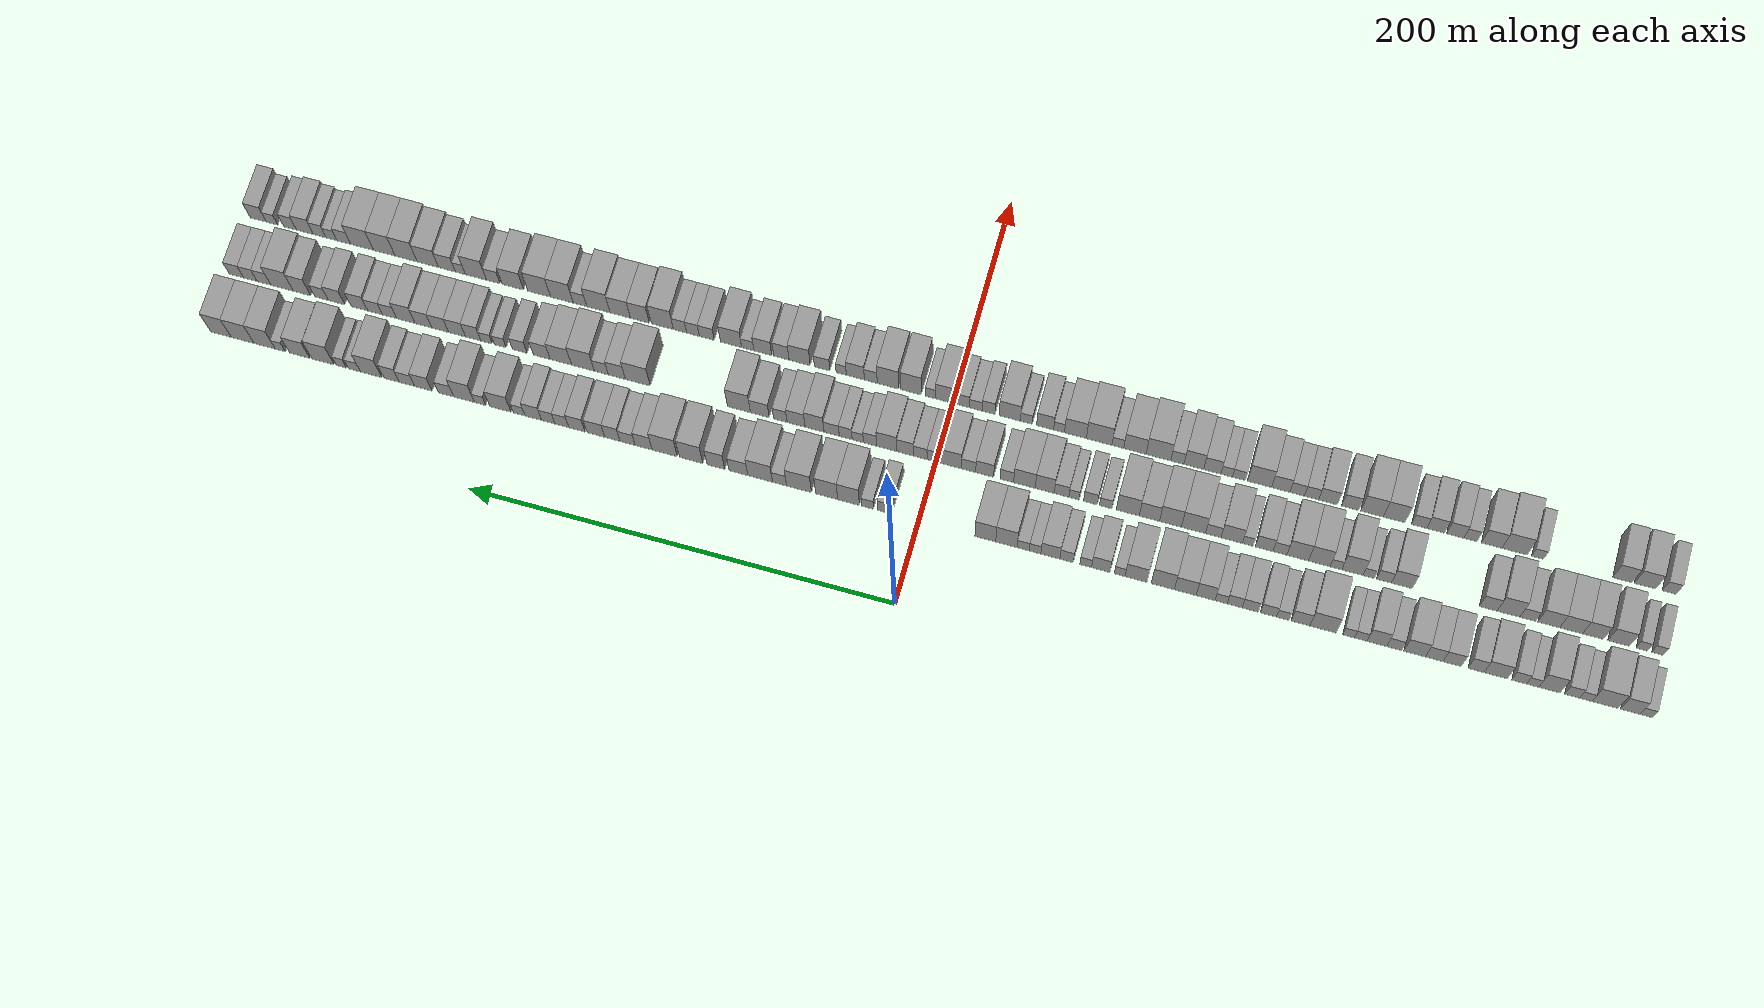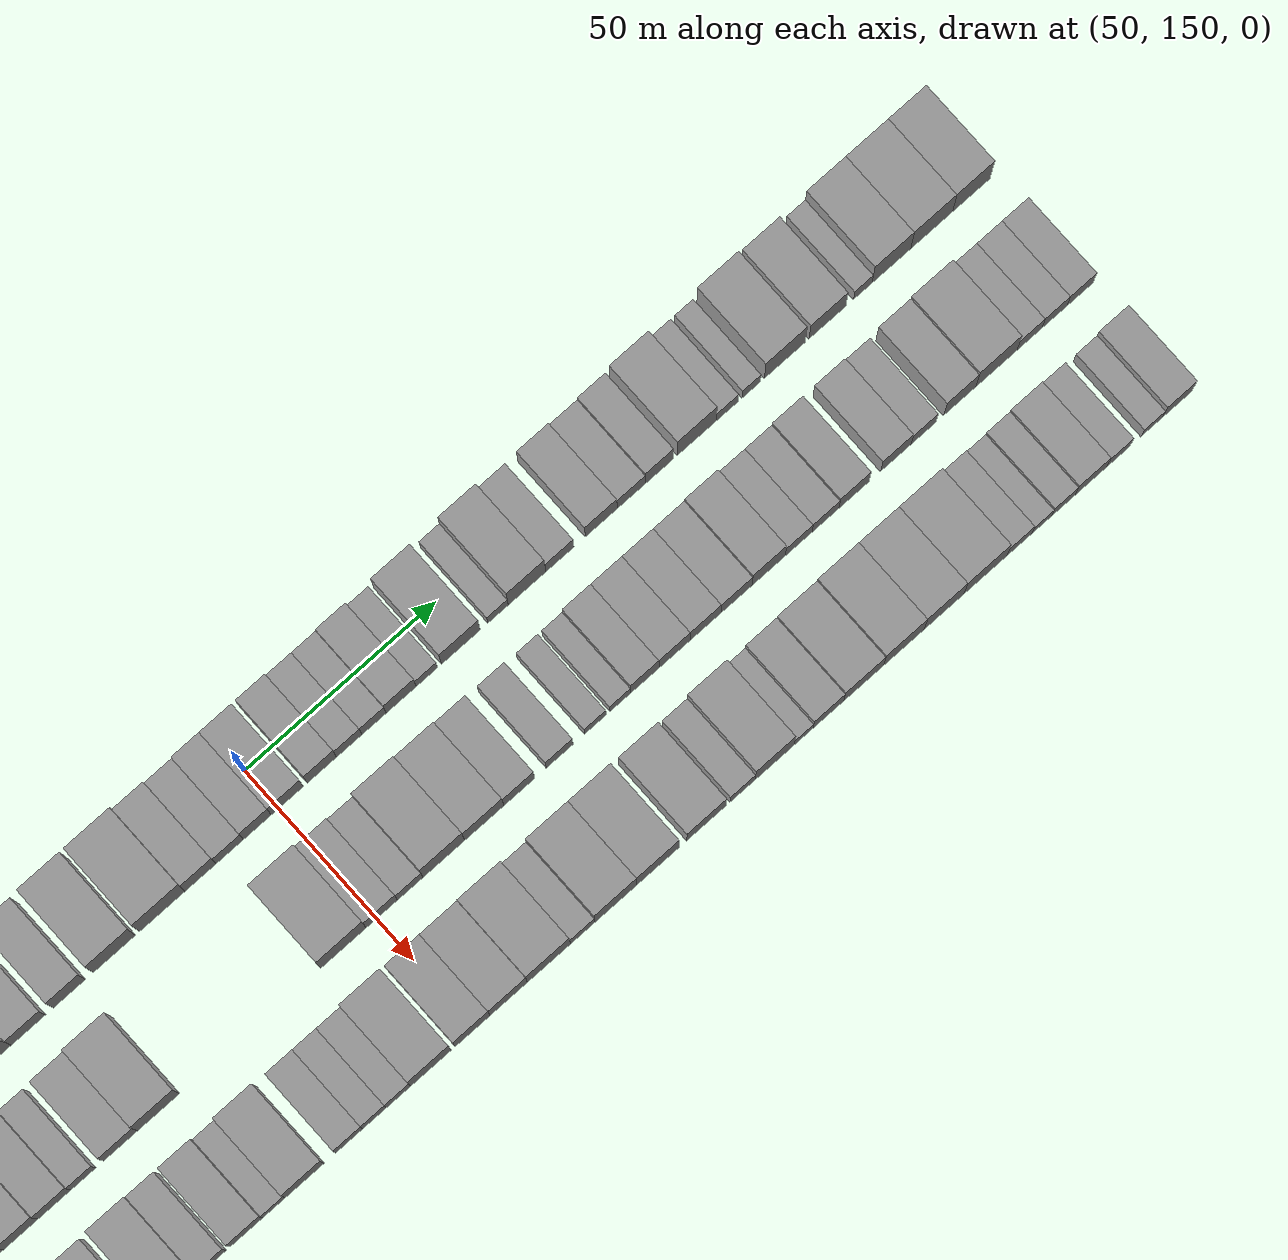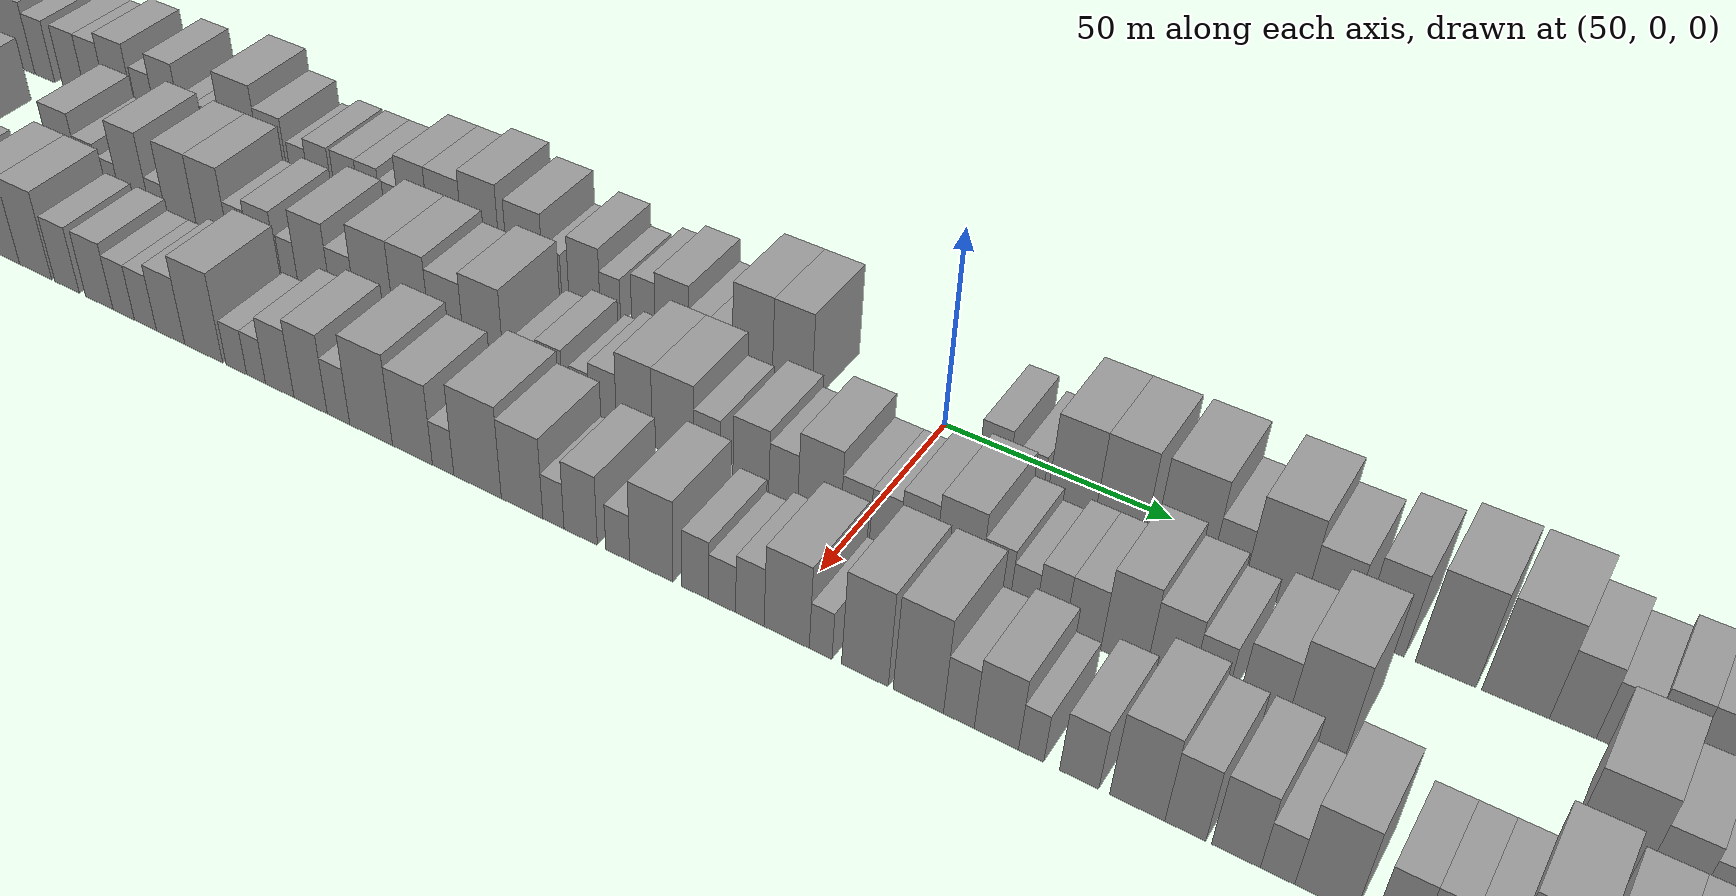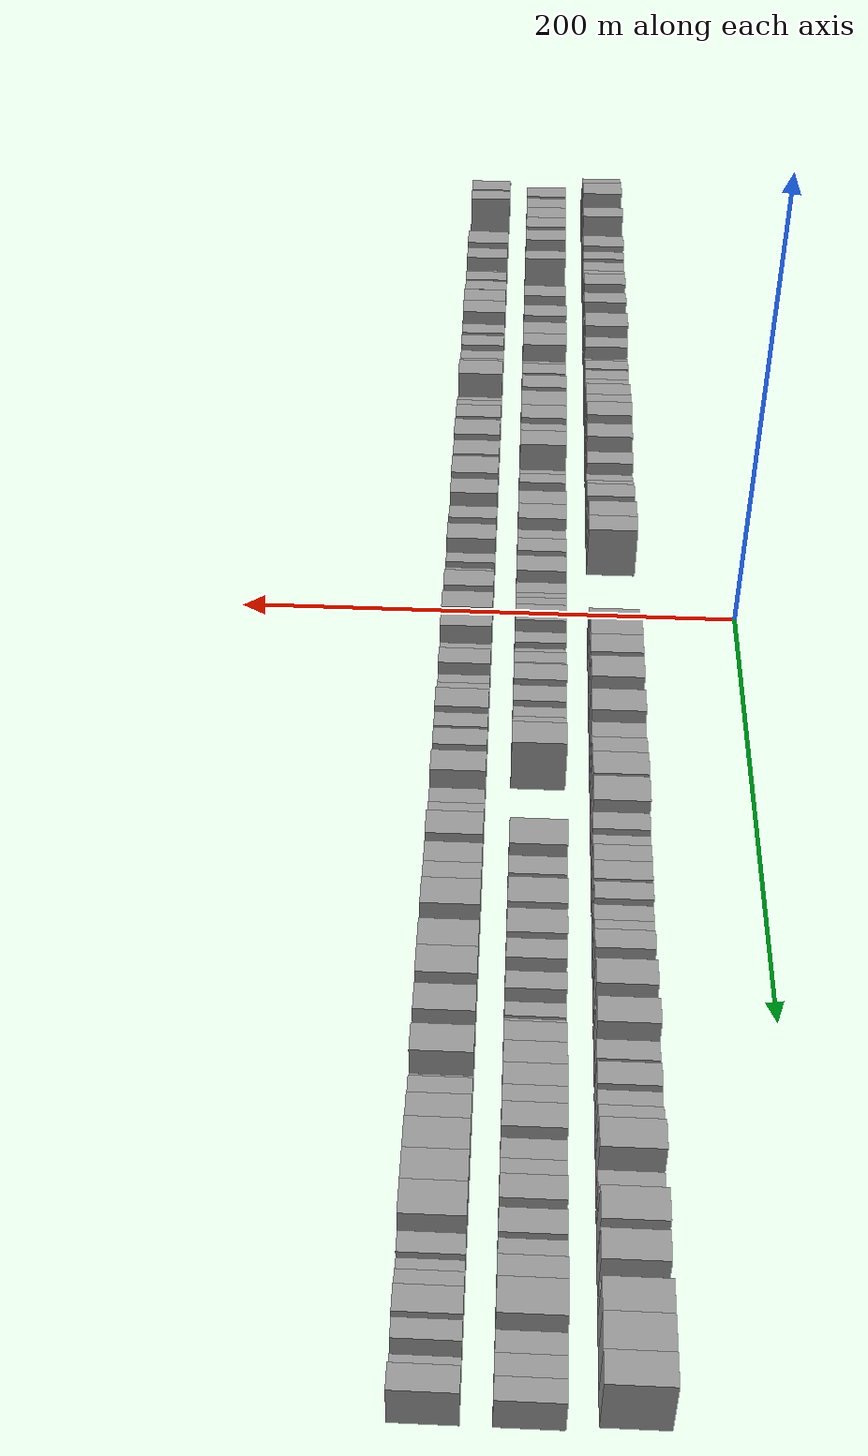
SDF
<sdf version="1.6">
 <world name="default">
  <scene>
   <sky><clouds><speed>12</speed></clouds></sky>
   <ambient>0.4 0.4 0.4 1</ambient>
   <background>0.7 0.7 0.7 1</background>
   <shadows>1</shadows>
  </scene>
  <gravity>0 0 -9.8066</gravity>
  <magnetic_field>6e-06 2.3e-05 -4.2e-05</magnetic_field>
  <physics default="0" name="default_physics" type="ode">
   <ode>
    <solver>
     <type>quick</type>
     <iters>10</iters>
     <sor>1.0</sor>
     <use_dynamic_moi_rescaling>0</use_dynamic_moi_rescaling>
    </solver>
    <constraints>
     <cfm>0</cfm>
     <erp>0.2</erp>
     <contact_max_correcting_vel>100</contact_max_correcting_vel>
     <contact_surface_layer>0.001</contact_surface_layer>
    </constraints>
   </ode>
   <max_step_size>0.004</max_step_size>
   <real_time_factor>1</real_time_factor>
   <real_time_update_rate>250</real_time_update_rate>
  </physics>
  <light name="sun" type="directional">
   <pose>0 0 10 0 0 0</pose>
   <diffuse>0.8 0.8 0.8 1</diffuse>
   <specular>0.2 0.2 0.2 1</specular>
   <attenuation>
    <range>1000</range>
    <constant>0.9</constant>
    <linear>0.01</linear>
    <quadratic>0.001</quadratic>
   </attenuation>
   <direction>-0.5 0.1 -0.9</direction>
  </light>
  <model name="building_1">
   <static>1</static>
   <pose>50.0000 -333.1980 0 0.000000 0.000000 0.000000</pose>
   <link name="link">
    <pose>0 0 6.00 0 0 0</pose>
    <collision name="collision"><geometry><box><size>20.0000 5.6040 12.0000</size></box></geometry></collision>
    <visual name="visual">
     <cast_shadows>0</cast_shadows>
     <geometry><box><size>20.0000 5.6040 12.0000</size></box></geometry>
     <material>
      <script>
       <uri>model://grey_wall/materials/scripts</uri>
       <uri>model://grey_wall/materials/textures</uri>
       <name>vrc/grey_wall</name>
      </script>
     </material>
    </visual>
   </link>
  </model>
  <model name="building_2">
   <static>1</static>
   <pose>50.0000 -325.9959 0 0.000000 0.000000 0.000000</pose>
   <link name="link">
    <pose>0 0 10.50 0 0 0</pose>
    <collision name="collision"><geometry><box><size>20.0000 8.8002 21.0000</size></box></geometry></collision>
    <visual name="visual">
     <cast_shadows>0</cast_shadows>
     <geometry><box><size>20.0000 8.8002 21.0000</size></box></geometry>
     <material>
      <script>
       <uri>model://grey_wall/materials/scripts</uri>
       <uri>model://grey_wall/materials/textures</uri>
       <name>vrc/grey_wall</name>
      </script>
     </material>
    </visual>
   </link>
  </model>
  <model name="building_3">
   <static>1</static>
   <pose>50.0000 -314.6749 0 0.000000 0.000000 0.000000</pose>
   <link name="link">
    <pose>0 0 12.00 0 0 0</pose>
    <collision name="collision"><geometry><box><size>20.0000 11.8418 24.0000</size></box></geometry></collision>
    <visual name="visual">
     <cast_shadows>0</cast_shadows>
     <geometry><box><size>20.0000 11.8418 24.0000</size></box></geometry>
     <material>
      <script>
       <uri>model://grey_wall/materials/scripts</uri>
       <uri>model://grey_wall/materials/textures</uri>
       <name>vrc/grey_wall</name>
      </script>
     </material>
    </visual>
   </link>
  </model>
  <model name="building_4">
   <static>1</static>
   <pose>50.0000 -306.0042 0 0.000000 0.000000 0.000000</pose>
   <link name="link">
    <pose>0 0 6.00 0 0 0</pose>
    <collision name="collision"><geometry><box><size>20.0000 5.4996 12.0000</size></box></geometry></collision>
    <visual name="visual">
     <cast_shadows>0</cast_shadows>
     <geometry><box><size>20.0000 5.4996 12.0000</size></box></geometry>
     <material>
      <script>
       <uri>model://grey_wall/materials/scripts</uri>
       <uri>model://grey_wall/materials/textures</uri>
       <name>vrc/grey_wall</name>
      </script>
     </material>
    </visual>
   </link>
  </model>
  <model name="building_5">
   <static>1</static>
   <pose>50.0000 -299.8403 0 0.000000 0.000000 0.000000</pose>
   <link name="link">
    <pose>0 0 7.50 0 0 0</pose>
    <collision name="collision"><geometry><box><size>20.0000 6.8281 15.0000</size></box></geometry></collision>
    <visual name="visual">
     <cast_shadows>0</cast_shadows>
     <geometry><box><size>20.0000 6.8281 15.0000</size></box></geometry>
     <material>
      <script>
       <uri>model://grey_wall/materials/scripts</uri>
       <uri>model://grey_wall/materials/textures</uri>
       <name>vrc/grey_wall</name>
      </script>
     </material>
    </visual>
   </link>
  </model>
  <model name="building_6">
   <static>1</static>
   <pose>50.0000 -289.6223 0 0.000000 0.000000 0.000000</pose>
   <link name="link">
    <pose>0 0 12.00 0 0 0</pose>
    <collision name="collision"><geometry><box><size>20.0000 9.6079 24.0000</size></box></geometry></collision>
    <visual name="visual">
     <cast_shadows>0</cast_shadows>
     <geometry><box><size>20.0000 9.6079 24.0000</size></box></geometry>
     <material>
      <script>
       <uri>model://grey_wall/materials/scripts</uri>
       <uri>model://grey_wall/materials/textures</uri>
       <name>vrc/grey_wall</name>
      </script>
     </material>
    </visual>
   </link>
  </model>
  <model name="building_7">
   <static>1</static>
   <pose>50.0000 -282.0489 0 0.000000 0.000000 0.000000</pose>
   <link name="link">
    <pose>0 0 6.00 0 0 0</pose>
    <collision name="collision"><geometry><box><size>20.0000 5.5390 12.0000</size></box></geometry></collision>
    <visual name="visual">
     <cast_shadows>0</cast_shadows>
     <geometry><box><size>20.0000 5.5390 12.0000</size></box></geometry>
     <material>
      <script>
       <uri>model://grey_wall/materials/scripts</uri>
       <uri>model://grey_wall/materials/textures</uri>
       <name>vrc/grey_wall</name>
      </script>
     </material>
    </visual>
   </link>
  </model>
  <model name="building_8">
   <static>1</static>
   <pose>50.0000 -275.9186 0 0.000000 0.000000 0.000000</pose>
   <link name="link">
    <pose>0 0 7.50 0 0 0</pose>
    <collision name="collision"><geometry><box><size>20.0000 6.7216 15.0000</size></box></geometry></collision>
    <visual name="visual">
     <cast_shadows>0</cast_shadows>
     <geometry><box><size>20.0000 6.7216 15.0000</size></box></geometry>
     <material>
      <script>
       <uri>model://grey_wall/materials/scripts</uri>
       <uri>model://grey_wall/materials/textures</uri>
       <name>vrc/grey_wall</name>
      </script>
     </material>
    </visual>
   </link>
  </model>
  <model name="building_9">
   <static>1</static>
   <pose>50.0000 -265.3210 0 0.000000 0.000000 0.000000</pose>
   <link name="link">
    <pose>0 0 10.50 0 0 0</pose>
    <collision name="collision"><geometry><box><size>20.0000 10.4738 21.0000</size></box></geometry></collision>
    <visual name="visual">
     <cast_shadows>0</cast_shadows>
     <geometry><box><size>20.0000 10.4738 21.0000</size></box></geometry>
     <material>
      <script>
       <uri>model://grey_wall/materials/scripts</uri>
       <uri>model://grey_wall/materials/textures</uri>
       <name>vrc/grey_wall</name>
      </script>
     </material>
    </visual>
   </link>
  </model>
  <model name="building_10">
   <static>1</static>
   <pose>50.0000 -256.4147 0 0.000000 0.000000 0.000000</pose>
   <link name="link">
    <pose>0 0 9.00 0 0 0</pose>
    <collision name="collision"><geometry><box><size>20.0000 7.3387 18.0000</size></box></geometry></collision>
    <visual name="visual">
     <cast_shadows>0</cast_shadows>
     <geometry><box><size>20.0000 7.3387 18.0000</size></box></geometry>
     <material>
      <script>
       <uri>model://grey_wall/materials/scripts</uri>
       <uri>model://grey_wall/materials/textures</uri>
       <name>vrc/grey_wall</name>
      </script>
     </material>
    </visual>
   </link>
  </model>
  <model name="building_11">
   <static>1</static>
   <pose>50.0000 -245.5799 0 0.000000 0.000000 0.000000</pose>
   <link name="link">
    <pose>0 0 9.00 0 0 0</pose>
    <collision name="collision"><geometry><box><size>20.0000 8.3308 18.0000</size></box></geometry></collision>
    <visual name="visual">
     <cast_shadows>0</cast_shadows>
     <geometry><box><size>20.0000 8.3308 18.0000</size></box></geometry>
     <material>
      <script>
       <uri>model://grey_wall/materials/scripts</uri>
       <uri>model://grey_wall/materials/textures</uri>
       <name>vrc/grey_wall</name>
      </script>
     </material>
    </visual>
   </link>
  </model>
  <model name="building_12">
   <static>1</static>
   <pose>50.0000 -237.4106 0 0.000000 0.000000 0.000000</pose>
   <link name="link">
    <pose>0 0 9.00 0 0 0</pose>
    <collision name="collision"><geometry><box><size>20.0000 8.0078 18.0000</size></box></geometry></collision>
    <visual name="visual">
     <cast_shadows>0</cast_shadows>
     <geometry><box><size>20.0000 8.0078 18.0000</size></box></geometry>
     <material>
      <script>
       <uri>model://grey_wall/materials/scripts</uri>
       <uri>model://grey_wall/materials/textures</uri>
       <name>vrc/grey_wall</name>
      </script>
     </material>
    </visual>
   </link>
  </model>
  <model name="building_13">
   <static>1</static>
   <pose>50.0000 -228.5051 0 0.000000 0.000000 0.000000</pose>
   <link name="link">
    <pose>0 0 10.50 0 0 0</pose>
    <collision name="collision"><geometry><box><size>20.0000 9.8033 21.0000</size></box></geometry></collision>
    <visual name="visual">
     <cast_shadows>0</cast_shadows>
     <geometry><box><size>20.0000 9.8033 21.0000</size></box></geometry>
     <material>
      <script>
       <uri>model://grey_wall/materials/scripts</uri>
       <uri>model://grey_wall/materials/textures</uri>
       <name>vrc/grey_wall</name>
      </script>
     </material>
    </visual>
   </link>
  </model>
  <model name="building_14">
   <static>1</static>
   <pose>50.0000 -219.2207 0 0.000000 0.000000 0.000000</pose>
   <link name="link">
    <pose>0 0 7.50 0 0 0</pose>
    <collision name="collision"><geometry><box><size>20.0000 6.7656 15.0000</size></box></geometry></collision>
    <visual name="visual">
     <cast_shadows>0</cast_shadows>
     <geometry><box><size>20.0000 6.7656 15.0000</size></box></geometry>
     <material>
      <script>
       <uri>model://grey_wall/materials/scripts</uri>
       <uri>model://grey_wall/materials/textures</uri>
       <name>vrc/grey_wall</name>
      </script>
     </material>
    </visual>
   </link>
  </model>
  <model name="building_15">
   <static>1</static>
   <pose>50.0000 -211.3232 0 0.000000 0.000000 0.000000</pose>
   <link name="link">
    <pose>0 0 10.50 0 0 0</pose>
    <collision name="collision"><geometry><box><size>20.0000 9.0295 21.0000</size></box></geometry></collision>
    <visual name="visual">
     <cast_shadows>0</cast_shadows>
     <geometry><box><size>20.0000 9.0295 21.0000</size></box></geometry>
     <material>
      <script>
       <uri>model://grey_wall/materials/scripts</uri>
       <uri>model://grey_wall/materials/textures</uri>
       <name>vrc/grey_wall</name>
      </script>
     </material>
    </visual>
   </link>
  </model>
  <model name="building_16">
   <static>1</static>
   <pose>50.0000 -203.9540 0 0.000000 0.000000 0.000000</pose>
   <link name="link">
    <pose>0 0 6.00 0 0 0</pose>
    <collision name="collision"><geometry><box><size>20.0000 5.7088 12.0000</size></box></geometry></collision>
    <visual name="visual">
     <cast_shadows>0</cast_shadows>
     <geometry><box><size>20.0000 5.7088 12.0000</size></box></geometry>
     <material>
      <script>
       <uri>model://grey_wall/materials/scripts</uri>
       <uri>model://grey_wall/materials/textures</uri>
       <name>vrc/grey_wall</name>
      </script>
     </material>
    </visual>
   </link>
  </model>
  <model name="building_17">
   <static>1</static>
   <pose>50.0000 -198.4020 0 0.000000 0.000000 0.000000</pose>
   <link name="link">
    <pose>0 0 6.00 0 0 0</pose>
    <collision name="collision"><geometry><box><size>20.0000 5.3952 12.0000</size></box></geometry></collision>
    <visual name="visual">
     <cast_shadows>0</cast_shadows>
     <geometry><box><size>20.0000 5.3952 12.0000</size></box></geometry>
     <material>
      <script>
       <uri>model://grey_wall/materials/scripts</uri>
       <uri>model://grey_wall/materials/textures</uri>
       <name>vrc/grey_wall</name>
      </script>
     </material>
    </visual>
   </link>
  </model>
  <model name="building_18">
   <static>1</static>
   <pose>50.0000 -186.7552 0 0.000000 0.000000 0.000000</pose>
   <link name="link">
    <pose>0 0 12.00 0 0 0</pose>
    <collision name="collision"><geometry><box><size>20.0000 11.8984 24.0000</size></box></geometry></collision>
    <visual name="visual">
     <cast_shadows>0</cast_shadows>
     <geometry><box><size>20.0000 11.8984 24.0000</size></box></geometry>
     <material>
      <script>
       <uri>model://grey_wall/materials/scripts</uri>
       <uri>model://grey_wall/materials/textures</uri>
       <name>vrc/grey_wall</name>
      </script>
     </material>
    </visual>
   </link>
  </model>
  <model name="building_19">
   <static>1</static>
   <pose>50.0000 -176.4865 0 0.000000 0.000000 0.000000</pose>
   <link name="link">
    <pose>0 0 9.00 0 0 0</pose>
    <collision name="collision"><geometry><box><size>20.0000 8.6390 18.0000</size></box></geometry></collision>
    <visual name="visual">
     <cast_shadows>0</cast_shadows>
     <geometry><box><size>20.0000 8.6390 18.0000</size></box></geometry>
     <material>
      <script>
       <uri>model://grey_wall/materials/scripts</uri>
       <uri>model://grey_wall/materials/textures</uri>
       <name>vrc/grey_wall</name>
      </script>
     </material>
    </visual>
   </link>
  </model>
  <model name="building_20">
   <static>1</static>
   <pose>50.0000 -168.3117 0 0.000000 0.000000 0.000000</pose>
   <link name="link">
    <pose>0 0 6.00 0 0 0</pose>
    <collision name="collision"><geometry><box><size>20.0000 5.7107 12.0000</size></box></geometry></collision>
    <visual name="visual">
     <cast_shadows>0</cast_shadows>
     <geometry><box><size>20.0000 5.7107 12.0000</size></box></geometry>
     <material>
      <script>
       <uri>model://grey_wall/materials/scripts</uri>
       <uri>model://grey_wall/materials/textures</uri>
       <name>vrc/grey_wall</name>
      </script>
     </material>
    </visual>
   </link>
  </model>
  <model name="building_21">
   <static>1</static>
   <pose>50.0000 -161.7797 0 0.000000 0.000000 0.000000</pose>
   <link name="link">
    <pose>0 0 7.50 0 0 0</pose>
    <collision name="collision"><geometry><box><size>20.0000 7.3533 15.0000</size></box></geometry></collision>
    <visual name="visual">
     <cast_shadows>0</cast_shadows>
     <geometry><box><size>20.0000 7.3533 15.0000</size></box></geometry>
     <material>
      <script>
       <uri>model://grey_wall/materials/scripts</uri>
       <uri>model://grey_wall/materials/textures</uri>
       <name>vrc/grey_wall</name>
      </script>
     </material>
    </visual>
   </link>
  </model>
  <model name="building_22">
   <static>1</static>
   <pose>50.0000 -153.3849 0 0.000000 0.000000 0.000000</pose>
   <link name="link">
    <pose>0 0 7.50 0 0 0</pose>
    <collision name="collision"><geometry><box><size>20.0000 7.4364 15.0000</size></box></geometry></collision>
    <visual name="visual">
     <cast_shadows>0</cast_shadows>
     <geometry><box><size>20.0000 7.4364 15.0000</size></box></geometry>
     <material>
      <script>
       <uri>model://grey_wall/materials/scripts</uri>
       <uri>model://grey_wall/materials/textures</uri>
       <name>vrc/grey_wall</name>
      </script>
     </material>
    </visual>
   </link>
  </model>
  <model name="building_23">
   <static>1</static>
   <pose>50.0000 -146.2702 0 0.000000 0.000000 0.000000</pose>
   <link name="link">
    <pose>0 0 7.50 0 0 0</pose>
    <collision name="collision"><geometry><box><size>20.0000 6.7929 15.0000</size></box></geometry></collision>
    <visual name="visual">
     <cast_shadows>0</cast_shadows>
     <geometry><box><size>20.0000 6.7929 15.0000</size></box></geometry>
     <material>
      <script>
       <uri>model://grey_wall/materials/scripts</uri>
       <uri>model://grey_wall/materials/textures</uri>
       <name>vrc/grey_wall</name>
      </script>
     </material>
    </visual>
   </link>
  </model>
  <model name="building_24">
   <static>1</static>
   <pose>50.0000 -140.0575 0 0.000000 0.000000 0.000000</pose>
   <link name="link">
    <pose>0 0 6.00 0 0 0</pose>
    <collision name="collision"><geometry><box><size>20.0000 5.6326 12.0000</size></box></geometry></collision>
    <visual name="visual">
     <cast_shadows>0</cast_shadows>
     <geometry><box><size>20.0000 5.6326 12.0000</size></box></geometry>
     <material>
      <script>
       <uri>model://grey_wall/materials/scripts</uri>
       <uri>model://grey_wall/materials/textures</uri>
       <name>vrc/grey_wall</name>
      </script>
     </material>
    </visual>
   </link>
  </model>
  <model name="building_25">
   <static>1</static>
   <pose>50.0000 -132.8841 0 0.000000 0.000000 0.000000</pose>
   <link name="link">
    <pose>0 0 10.50 0 0 0</pose>
    <collision name="collision"><geometry><box><size>20.0000 8.7143 21.0000</size></box></geometry></collision>
    <visual name="visual">
     <cast_shadows>0</cast_shadows>
     <geometry><box><size>20.0000 8.7143 21.0000</size></box></geometry>
     <material>
      <script>
       <uri>model://grey_wall/materials/scripts</uri>
       <uri>model://grey_wall/materials/textures</uri>
       <name>vrc/grey_wall</name>
      </script>
     </material>
    </visual>
   </link>
  </model>
  <model name="building_26">
   <static>1</static>
   <pose>50.0000 -123.5216 0 0.000000 0.000000 0.000000</pose>
   <link name="link">
    <pose>0 0 10.50 0 0 0</pose>
    <collision name="collision"><geometry><box><size>20.0000 10.0106 21.0000</size></box></geometry></collision>
    <visual name="visual">
     <cast_shadows>0</cast_shadows>
     <geometry><box><size>20.0000 10.0106 21.0000</size></box></geometry>
     <material>
      <script>
       <uri>model://grey_wall/materials/scripts</uri>
       <uri>model://grey_wall/materials/textures</uri>
       <name>vrc/grey_wall</name>
      </script>
     </material>
    </visual>
   </link>
  </model>
  <model name="building_27">
   <static>1</static>
   <pose>50.0000 -113.2115 0 0.000000 0.000000 0.000000</pose>
   <link name="link">
    <pose>0 0 12.00 0 0 0</pose>
    <collision name="collision"><geometry><box><size>20.0000 10.6096 24.0000</size></box></geometry></collision>
    <visual name="visual">
     <cast_shadows>0</cast_shadows>
     <geometry><box><size>20.0000 10.6096 24.0000</size></box></geometry>
     <material>
      <script>
       <uri>model://grey_wall/materials/scripts</uri>
       <uri>model://grey_wall/materials/textures</uri>
       <name>vrc/grey_wall</name>
      </script>
     </material>
    </visual>
   </link>
  </model>
  <model name="building_28">
   <static>1</static>
   <pose>50.0000 -100.8549 0 0.000000 0.000000 0.000000</pose>
   <link name="link">
    <pose>0 0 10.50 0 0 0</pose>
    <collision name="collision"><geometry><box><size>20.0000 10.1035 21.0000</size></box></geometry></collision>
    <visual name="visual">
     <cast_shadows>0</cast_shadows>
     <geometry><box><size>20.0000 10.1035 21.0000</size></box></geometry>
     <material>
      <script>
       <uri>model://grey_wall/materials/scripts</uri>
       <uri>model://grey_wall/materials/textures</uri>
       <name>vrc/grey_wall</name>
      </script>
     </material>
    </visual>
   </link>
  </model>
  <model name="building_29">
   <static>1</static>
   <pose>50.0000 -93.3208 0 0.000000 0.000000 0.000000</pose>
   <link name="link">
    <pose>0 0 6.00 0 0 0</pose>
    <collision name="collision"><geometry><box><size>20.0000 4.9647 12.0000</size></box></geometry></collision>
    <visual name="visual">
     <cast_shadows>0</cast_shadows>
     <geometry><box><size>20.0000 4.9647 12.0000</size></box></geometry>
     <material>
      <script>
       <uri>model://grey_wall/materials/scripts</uri>
       <uri>model://grey_wall/materials/textures</uri>
       <name>vrc/grey_wall</name>
      </script>
     </material>
    </visual>
   </link>
  </model>
  <model name="building_30">
   <static>1</static>
   <pose>50.0000 -84.5850 0 0.000000 0.000000 0.000000</pose>
   <link name="link">
    <pose>0 0 9.00 0 0 0</pose>
    <collision name="collision"><geometry><box><size>20.0000 8.5069 18.0000</size></box></geometry></collision>
    <visual name="visual">
     <cast_shadows>0</cast_shadows>
     <geometry><box><size>20.0000 8.5069 18.0000</size></box></geometry>
     <material>
      <script>
       <uri>model://grey_wall/materials/scripts</uri>
       <uri>model://grey_wall/materials/textures</uri>
       <name>vrc/grey_wall</name>
      </script>
     </material>
    </visual>
   </link>
  </model>
  <model name="building_31">
   <static>1</static>
   <pose>50.0000 -77.5886 0 0.000000 0.000000 0.000000</pose>
   <link name="link">
    <pose>0 0 6.00 0 0 0</pose>
    <collision name="collision"><geometry><box><size>20.0000 5.4859 12.0000</size></box></geometry></collision>
    <visual name="visual">
     <cast_shadows>0</cast_shadows>
     <geometry><box><size>20.0000 5.4859 12.0000</size></box></geometry>
     <material>
      <script>
       <uri>model://grey_wall/materials/scripts</uri>
       <uri>model://grey_wall/materials/textures</uri>
       <name>vrc/grey_wall</name>
      </script>
     </material>
    </visual>
   </link>
  </model>
  <model name="building_32">
   <static>1</static>
   <pose>50.0000 -68.7563 0 0.000000 0.000000 0.000000</pose>
   <link name="link">
    <pose>0 0 7.50 0 0 0</pose>
    <collision name="collision"><geometry><box><size>20.0000 6.1787 15.0000</size></box></geometry></collision>
    <visual name="visual">
     <cast_shadows>0</cast_shadows>
     <geometry><box><size>20.0000 6.1787 15.0000</size></box></geometry>
     <material>
      <script>
       <uri>model://grey_wall/materials/scripts</uri>
       <uri>model://grey_wall/materials/textures</uri>
       <name>vrc/grey_wall</name>
      </script>
     </material>
    </visual>
   </link>
  </model>
  <model name="building_33">
   <static>1</static>
   <pose>50.0000 -61.2406 0 0.000000 0.000000 0.000000</pose>
   <link name="link">
    <pose>0 0 9.00 0 0 0</pose>
    <collision name="collision"><geometry><box><size>20.0000 8.8527 18.0000</size></box></geometry></collision>
    <visual name="visual">
     <cast_shadows>0</cast_shadows>
     <geometry><box><size>20.0000 8.8527 18.0000</size></box></geometry>
     <material>
      <script>
       <uri>model://grey_wall/materials/scripts</uri>
       <uri>model://grey_wall/materials/textures</uri>
       <name>vrc/grey_wall</name>
      </script>
     </material>
    </visual>
   </link>
  </model>
  <model name="building_34">
   <static>1</static>
   <pose>50.0000 -54.1243 0 0.000000 0.000000 0.000000</pose>
   <link name="link">
    <pose>0 0 6.00 0 0 0</pose>
    <collision name="collision"><geometry><box><size>20.0000 5.3798 12.0000</size></box></geometry></collision>
    <visual name="visual">
     <cast_shadows>0</cast_shadows>
     <geometry><box><size>20.0000 5.3798 12.0000</size></box></geometry>
     <material>
      <script>
       <uri>model://grey_wall/materials/scripts</uri>
       <uri>model://grey_wall/materials/textures</uri>
       <name>vrc/grey_wall</name>
      </script>
     </material>
    </visual>
   </link>
  </model>
  <model name="building_35">
   <static>1</static>
   <pose>50.0000 -48.6265 0 0.000000 0.000000 0.000000</pose>
   <link name="link">
    <pose>0 0 6.00 0 0 0</pose>
    <collision name="collision"><geometry><box><size>20.0000 5.6158 12.0000</size></box></geometry></collision>
    <visual name="visual">
     <cast_shadows>0</cast_shadows>
     <geometry><box><size>20.0000 5.6158 12.0000</size></box></geometry>
     <material>
      <script>
       <uri>model://grey_wall/materials/scripts</uri>
       <uri>model://grey_wall/materials/textures</uri>
       <name>vrc/grey_wall</name>
      </script>
     </material>
    </visual>
   </link>
  </model>
  <model name="building_36">
   <static>1</static>
   <pose>50.0000 -40.8374 0 0.000000 0.000000 0.000000</pose>
   <link name="link">
    <pose>0 0 12.00 0 0 0</pose>
    <collision name="collision"><geometry><box><size>20.0000 9.9623 24.0000</size></box></geometry></collision>
    <visual name="visual">
     <cast_shadows>0</cast_shadows>
     <geometry><box><size>20.0000 9.9623 24.0000</size></box></geometry>
     <material>
      <script>
       <uri>model://grey_wall/materials/scripts</uri>
       <uri>model://grey_wall/materials/textures</uri>
       <name>vrc/grey_wall</name>
      </script>
     </material>
    </visual>
   </link>
  </model>
  <model name="building_37">
   <static>1</static>
   <pose>50.0000 -31.0050 0 0.000000 0.000000 0.000000</pose>
   <link name="link">
    <pose>0 0 12.00 0 0 0</pose>
    <collision name="collision"><geometry><box><size>20.0000 9.7026 24.0000</size></box></geometry></collision>
    <visual name="visual">
     <cast_shadows>0</cast_shadows>
     <geometry><box><size>20.0000 9.7026 24.0000</size></box></geometry>
     <material>
      <script>
       <uri>model://grey_wall/materials/scripts</uri>
       <uri>model://grey_wall/materials/textures</uri>
       <name>vrc/grey_wall</name>
      </script>
     </material>
    </visual>
   </link>
  </model>
  <model name="building_38">
   <static>1</static>
   <pose>50.0000 15.8936 0 0.000000 0.000000 0.000000</pose>
   <link name="link">
    <pose>0 0 7.50 0 0 0</pose>
    <collision name="collision"><geometry><box><size>20.0000 6.6982 15.0000</size></box></geometry></collision>
    <visual name="visual">
     <cast_shadows>0</cast_shadows>
     <geometry><box><size>20.0000 6.6982 15.0000</size></box></geometry>
     <material>
      <script>
       <uri>model://grey_wall/materials/scripts</uri>
       <uri>model://grey_wall/materials/textures</uri>
       <name>vrc/grey_wall</name>
      </script>
     </material>
    </visual>
   </link>
  </model>
  <model name="building_39">
   <static>1</static>
   <pose>50.0000 24.0264 0 0.000000 0.000000 0.000000</pose>
   <link name="link">
    <pose>0 0 6.00 0 0 0</pose>
    <collision name="collision"><geometry><box><size>20.0000 5.5673 12.0000</size></box></geometry></collision>
    <visual name="visual">
     <cast_shadows>0</cast_shadows>
     <geometry><box><size>20.0000 5.5673 12.0000</size></box></geometry>
     <material>
      <script>
       <uri>model://grey_wall/materials/scripts</uri>
       <uri>model://grey_wall/materials/textures</uri>
       <name>vrc/grey_wall</name>
      </script>
     </material>
    </visual>
   </link>
  </model>
  <model name="building_40">
   <static>1</static>
   <pose>50.0000 32.8881 0 0.000000 0.000000 0.000000</pose>
   <link name="link">
    <pose>0 0 12.00 0 0 0</pose>
    <collision name="collision"><geometry><box><size>20.0000 10.1561 24.0000</size></box></geometry></collision>
    <visual name="visual">
     <cast_shadows>0</cast_shadows>
     <geometry><box><size>20.0000 10.1561 24.0000</size></box></geometry>
     <material>
      <script>
       <uri>model://grey_wall/materials/scripts</uri>
       <uri>model://grey_wall/materials/textures</uri>
       <name>vrc/grey_wall</name>
      </script>
     </material>
    </visual>
   </link>
  </model>
  <model name="building_41">
   <static>1</static>
   <pose>50.0000 43.1462 0 0.000000 0.000000 0.000000</pose>
   <link name="link">
    <pose>0 0 12.00 0 0 0</pose>
    <collision name="collision"><geometry><box><size>20.0000 10.3601 24.0000</size></box></geometry></collision>
    <visual name="visual">
     <cast_shadows>0</cast_shadows>
     <geometry><box><size>20.0000 10.3601 24.0000</size></box></geometry>
     <material>
      <script>
       <uri>model://grey_wall/materials/scripts</uri>
       <uri>model://grey_wall/materials/textures</uri>
       <name>vrc/grey_wall</name>
      </script>
     </material>
    </visual>
   </link>
  </model>
  <model name="building_42">
   <static>1</static>
   <pose>50.0000 56.1803 0 0.000000 0.000000 0.000000</pose>
   <link name="link">
    <pose>0 0 12.00 0 0 0</pose>
    <collision name="collision"><geometry><box><size>20.0000 11.7080 24.0000</size></box></geometry></collision>
    <visual name="visual">
     <cast_shadows>0</cast_shadows>
     <geometry><box><size>20.0000 11.7080 24.0000</size></box></geometry>
     <material>
      <script>
       <uri>model://grey_wall/materials/scripts</uri>
       <uri>model://grey_wall/materials/textures</uri>
       <name>vrc/grey_wall</name>
      </script>
     </material>
    </visual>
   </link>
  </model>
  <model name="building_43">
   <static>1</static>
   <pose>50.0000 65.3462 0 0.000000 0.000000 0.000000</pose>
   <link name="link">
    <pose>0 0 7.50 0 0 0</pose>
    <collision name="collision"><geometry><box><size>20.0000 6.6238 15.0000</size></box></geometry></collision>
    <visual name="visual">
     <cast_shadows>0</cast_shadows>
     <geometry><box><size>20.0000 6.6238 15.0000</size></box></geometry>
     <material>
      <script>
       <uri>model://grey_wall/materials/scripts</uri>
       <uri>model://grey_wall/materials/textures</uri>
       <name>vrc/grey_wall</name>
      </script>
     </material>
    </visual>
   </link>
  </model>
  <model name="building_44">
   <static>1</static>
   <pose>50.0000 74.4359 0 0.000000 0.000000 0.000000</pose>
   <link name="link">
    <pose>0 0 12.00 0 0 0</pose>
    <collision name="collision"><geometry><box><size>20.0000 11.5555 24.0000</size></box></geometry></collision>
    <visual name="visual">
     <cast_shadows>0</cast_shadows>
     <geometry><box><size>20.0000 11.5555 24.0000</size></box></geometry>
     <material>
      <script>
       <uri>model://grey_wall/materials/scripts</uri>
       <uri>model://grey_wall/materials/textures</uri>
       <name>vrc/grey_wall</name>
      </script>
     </material>
    </visual>
   </link>
  </model>
  <model name="building_45">
   <static>1</static>
   <pose>50.0000 84.6736 0 0.000000 0.000000 0.000000</pose>
   <link name="link">
    <pose>0 0 9.00 0 0 0</pose>
    <collision name="collision"><geometry><box><size>20.0000 8.9198 18.0000</size></box></geometry></collision>
    <visual name="visual">
     <cast_shadows>0</cast_shadows>
     <geometry><box><size>20.0000 8.9198 18.0000</size></box></geometry>
     <material>
      <script>
       <uri>model://grey_wall/materials/scripts</uri>
       <uri>model://grey_wall/materials/textures</uri>
       <name>vrc/grey_wall</name>
      </script>
     </material>
    </visual>
   </link>
  </model>
  <model name="building_46">
   <static>1</static>
   <pose>50.0000 95.3387 0 0.000000 0.000000 0.000000</pose>
   <link name="link">
    <pose>0 0 10.50 0 0 0</pose>
    <collision name="collision"><geometry><box><size>20.0000 8.4104 21.0000</size></box></geometry></collision>
    <visual name="visual">
     <cast_shadows>0</cast_shadows>
     <geometry><box><size>20.0000 8.4104 21.0000</size></box></geometry>
     <material>
      <script>
       <uri>model://grey_wall/materials/scripts</uri>
       <uri>model://grey_wall/materials/textures</uri>
       <name>vrc/grey_wall</name>
      </script>
     </material>
    </visual>
   </link>
  </model>
  <model name="building_47">
   <static>1</static>
   <pose>50.0000 107.0612 0 0.000000 0.000000 0.000000</pose>
   <link name="link">
    <pose>0 0 12.00 0 0 0</pose>
    <collision name="collision"><geometry><box><size>20.0000 11.0347 24.0000</size></box></geometry></collision>
    <visual name="visual">
     <cast_shadows>0</cast_shadows>
     <geometry><box><size>20.0000 11.0347 24.0000</size></box></geometry>
     <material>
      <script>
       <uri>model://grey_wall/materials/scripts</uri>
       <uri>model://grey_wall/materials/textures</uri>
       <name>vrc/grey_wall</name>
      </script>
     </material>
    </visual>
   </link>
  </model>
  <model name="building_48">
   <static>1</static>
   <pose>50.0000 119.5464 0 0.000000 0.000000 0.000000</pose>
   <link name="link">
    <pose>0 0 12.00 0 0 0</pose>
    <collision name="collision"><geometry><box><size>20.0000 11.9357 24.0000</size></box></geometry></collision>
    <visual name="visual">
     <cast_shadows>0</cast_shadows>
     <geometry><box><size>20.0000 11.9357 24.0000</size></box></geometry>
     <material>
      <script>
       <uri>model://grey_wall/materials/scripts</uri>
       <uri>model://grey_wall/materials/textures</uri>
       <name>vrc/grey_wall</name>
      </script>
     </material>
    </visual>
   </link>
  </model>
  <model name="building_49">
   <static>1</static>
   <pose>50.0000 129.5451 0 0.000000 0.000000 0.000000</pose>
   <link name="link">
    <pose>0 0 9.00 0 0 0</pose>
    <collision name="collision"><geometry><box><size>20.0000 8.0616 18.0000</size></box></geometry></collision>
    <visual name="visual">
     <cast_shadows>0</cast_shadows>
     <geometry><box><size>20.0000 8.0616 18.0000</size></box></geometry>
     <material>
      <script>
       <uri>model://grey_wall/materials/scripts</uri>
       <uri>model://grey_wall/materials/textures</uri>
       <name>vrc/grey_wall</name>
      </script>
     </material>
    </visual>
   </link>
  </model>
  <model name="building_50">
   <static>1</static>
   <pose>50.0000 137.1619 0 0.000000 0.000000 0.000000</pose>
   <link name="link">
    <pose>0 0 7.50 0 0 0</pose>
    <collision name="collision"><geometry><box><size>20.0000 7.1721 15.0000</size></box></geometry></collision>
    <visual name="visual">
     <cast_shadows>0</cast_shadows>
     <geometry><box><size>20.0000 7.1721 15.0000</size></box></geometry>
     <material>
      <script>
       <uri>model://grey_wall/materials/scripts</uri>
       <uri>model://grey_wall/materials/textures</uri>
       <name>vrc/grey_wall</name>
      </script>
     </material>
    </visual>
   </link>
  </model>
  <model name="building_51">
   <static>1</static>
   <pose>50.0000 144.3890 0 0.000000 0.000000 0.000000</pose>
   <link name="link">
    <pose>0 0 9.00 0 0 0</pose>
    <collision name="collision"><geometry><box><size>20.0000 7.2822 18.0000</size></box></geometry></collision>
    <visual name="visual">
     <cast_shadows>0</cast_shadows>
     <geometry><box><size>20.0000 7.2822 18.0000</size></box></geometry>
     <material>
      <script>
       <uri>model://grey_wall/materials/scripts</uri>
       <uri>model://grey_wall/materials/textures</uri>
       <name>vrc/grey_wall</name>
      </script>
     </material>
    </visual>
   </link>
  </model>
  <model name="building_52">
   <static>1</static>
   <pose>50.0000 152.2373 0 0.000000 0.000000 0.000000</pose>
   <link name="link">
    <pose>0 0 9.00 0 0 0</pose>
    <collision name="collision"><geometry><box><size>20.0000 8.4143 18.0000</size></box></geometry></collision>
    <visual name="visual">
     <cast_shadows>0</cast_shadows>
     <geometry><box><size>20.0000 8.4143 18.0000</size></box></geometry>
     <material>
      <script>
       <uri>model://grey_wall/materials/scripts</uri>
       <uri>model://grey_wall/materials/textures</uri>
       <name>vrc/grey_wall</name>
      </script>
     </material>
    </visual>
   </link>
  </model>
  <model name="building_53">
   <static>1</static>
   <pose>50.0000 161.2836 0 0.000000 0.000000 0.000000</pose>
   <link name="link">
    <pose>0 0 9.00 0 0 0</pose>
    <collision name="collision"><geometry><box><size>20.0000 7.6783 18.0000</size></box></geometry></collision>
    <visual name="visual">
     <cast_shadows>0</cast_shadows>
     <geometry><box><size>20.0000 7.6783 18.0000</size></box></geometry>
     <material>
      <script>
       <uri>model://grey_wall/materials/scripts</uri>
       <uri>model://grey_wall/materials/textures</uri>
       <name>vrc/grey_wall</name>
      </script>
     </material>
    </visual>
   </link>
  </model>
  <model name="building_54">
   <static>1</static>
   <pose>50.0000 168.4406 0 0.000000 0.000000 0.000000</pose>
   <link name="link">
    <pose>0 0 7.50 0 0 0</pose>
    <collision name="collision"><geometry><box><size>20.0000 6.6355 15.0000</size></box></geometry></collision>
    <visual name="visual">
     <cast_shadows>0</cast_shadows>
     <geometry><box><size>20.0000 6.6355 15.0000</size></box></geometry>
     <material>
      <script>
       <uri>model://grey_wall/materials/scripts</uri>
       <uri>model://grey_wall/materials/textures</uri>
       <name>vrc/grey_wall</name>
      </script>
     </material>
    </visual>
   </link>
  </model>
  <model name="building_55">
   <static>1</static>
   <pose>50.0000 174.9485 0 0.000000 0.000000 0.000000</pose>
   <link name="link">
    <pose>0 0 7.50 0 0 0</pose>
    <collision name="collision"><geometry><box><size>20.0000 6.3804 15.0000</size></box></geometry></collision>
    <visual name="visual">
     <cast_shadows>0</cast_shadows>
     <geometry><box><size>20.0000 6.3804 15.0000</size></box></geometry>
     <material>
      <script>
       <uri>model://grey_wall/materials/scripts</uri>
       <uri>model://grey_wall/materials/textures</uri>
       <name>vrc/grey_wall</name>
      </script>
     </material>
    </visual>
   </link>
  </model>
  <model name="building_56">
   <static>1</static>
   <pose>50.0000 182.0688 0 0.000000 0.000000 0.000000</pose>
   <link name="link">
    <pose>0 0 9.00 0 0 0</pose>
    <collision name="collision"><geometry><box><size>20.0000 7.8603 18.0000</size></box></geometry></collision>
    <visual name="visual">
     <cast_shadows>0</cast_shadows>
     <geometry><box><size>20.0000 7.8603 18.0000</size></box></geometry>
     <material>
      <script>
       <uri>model://grey_wall/materials/scripts</uri>
       <uri>model://grey_wall/materials/textures</uri>
       <name>vrc/grey_wall</name>
      </script>
     </material>
    </visual>
   </link>
  </model>
  <model name="building_57">
   <static>1</static>
   <pose>50.0000 188.8283 0 0.000000 0.000000 0.000000</pose>
   <link name="link">
    <pose>0 0 6.00 0 0 0</pose>
    <collision name="collision"><geometry><box><size>20.0000 5.6586 12.0000</size></box></geometry></collision>
    <visual name="visual">
     <cast_shadows>0</cast_shadows>
     <geometry><box><size>20.0000 5.6586 12.0000</size></box></geometry>
     <material>
      <script>
       <uri>model://grey_wall/materials/scripts</uri>
       <uri>model://grey_wall/materials/textures</uri>
       <name>vrc/grey_wall</name>
      </script>
     </material>
    </visual>
   </link>
  </model>
  <model name="building_58">
   <static>1</static>
   <pose>50.0000 197.7413 0 0.000000 0.000000 0.000000</pose>
   <link name="link">
    <pose>0 0 10.50 0 0 0</pose>
    <collision name="collision"><geometry><box><size>20.0000 10.1673 21.0000</size></box></geometry></collision>
    <visual name="visual">
     <cast_shadows>0</cast_shadows>
     <geometry><box><size>20.0000 10.1673 21.0000</size></box></geometry>
     <material>
      <script>
       <uri>model://grey_wall/materials/scripts</uri>
       <uri>model://grey_wall/materials/textures</uri>
       <name>vrc/grey_wall</name>
      </script>
     </material>
    </visual>
   </link>
  </model>
  <model name="building_59">
   <static>1</static>
   <pose>50.0000 207.5146 0 0.000000 0.000000 0.000000</pose>
   <link name="link">
    <pose>0 0 6.00 0 0 0</pose>
    <collision name="collision"><geometry><box><size>20.0000 5.3793 12.0000</size></box></geometry></collision>
    <visual name="visual">
     <cast_shadows>0</cast_shadows>
     <geometry><box><size>20.0000 5.3793 12.0000</size></box></geometry>
     <material>
      <script>
       <uri>model://grey_wall/materials/scripts</uri>
       <uri>model://grey_wall/materials/textures</uri>
       <name>vrc/grey_wall</name>
      </script>
     </material>
    </visual>
   </link>
  </model>
  <model name="building_60">
   <static>1</static>
   <pose>50.0000 215.1342 0 0.000000 0.000000 0.000000</pose>
   <link name="link">
    <pose>0 0 12.00 0 0 0</pose>
    <collision name="collision"><geometry><box><size>20.0000 9.8598 24.0000</size></box></geometry></collision>
    <visual name="visual">
     <cast_shadows>0</cast_shadows>
     <geometry><box><size>20.0000 9.8598 24.0000</size></box></geometry>
     <material>
      <script>
       <uri>model://grey_wall/materials/scripts</uri>
       <uri>model://grey_wall/materials/textures</uri>
       <name>vrc/grey_wall</name>
      </script>
     </material>
    </visual>
   </link>
  </model>
  <model name="building_61">
   <static>1</static>
   <pose>50.0000 223.7643 0 0.000000 0.000000 0.000000</pose>
   <link name="link">
    <pose>0 0 7.50 0 0 0</pose>
    <collision name="collision"><geometry><box><size>20.0000 7.4004 15.0000</size></box></geometry></collision>
    <visual name="visual">
     <cast_shadows>0</cast_shadows>
     <geometry><box><size>20.0000 7.4004 15.0000</size></box></geometry>
     <material>
      <script>
       <uri>model://grey_wall/materials/scripts</uri>
       <uri>model://grey_wall/materials/textures</uri>
       <name>vrc/grey_wall</name>
      </script>
     </material>
    </visual>
   </link>
  </model>
  <model name="building_62">
   <static>1</static>
   <pose>50.0000 234.6617 0 0.000000 0.000000 0.000000</pose>
   <link name="link">
    <pose>0 0 9.00 0 0 0</pose>
    <collision name="collision"><geometry><box><size>20.0000 8.3944 18.0000</size></box></geometry></collision>
    <visual name="visual">
     <cast_shadows>0</cast_shadows>
     <geometry><box><size>20.0000 8.3944 18.0000</size></box></geometry>
     <material>
      <script>
       <uri>model://grey_wall/materials/scripts</uri>
       <uri>model://grey_wall/materials/textures</uri>
       <name>vrc/grey_wall</name>
      </script>
     </material>
    </visual>
   </link>
  </model>
  <model name="building_63">
   <static>1</static>
   <pose>50.0000 242.5920 0 0.000000 0.000000 0.000000</pose>
   <link name="link">
    <pose>0 0 7.50 0 0 0</pose>
    <collision name="collision"><geometry><box><size>20.0000 7.4664 15.0000</size></box></geometry></collision>
    <visual name="visual">
     <cast_shadows>0</cast_shadows>
     <geometry><box><size>20.0000 7.4664 15.0000</size></box></geometry>
     <material>
      <script>
       <uri>model://grey_wall/materials/scripts</uri>
       <uri>model://grey_wall/materials/textures</uri>
       <name>vrc/grey_wall</name>
      </script>
     </material>
    </visual>
   </link>
  </model>
  <model name="building_64">
   <static>1</static>
   <pose>50.0000 250.0155 0 0.000000 0.000000 0.000000</pose>
   <link name="link">
    <pose>0 0 9.00 0 0 0</pose>
    <collision name="collision"><geometry><box><size>20.0000 7.3805 18.0000</size></box></geometry></collision>
    <visual name="visual">
     <cast_shadows>0</cast_shadows>
     <geometry><box><size>20.0000 7.3805 18.0000</size></box></geometry>
     <material>
      <script>
       <uri>model://grey_wall/materials/scripts</uri>
       <uri>model://grey_wall/materials/textures</uri>
       <name>vrc/grey_wall</name>
      </script>
     </material>
    </visual>
   </link>
  </model>
  <model name="building_65">
   <static>1</static>
   <pose>50.0000 259.8513 0 0.000000 0.000000 0.000000</pose>
   <link name="link">
    <pose>0 0 12.00 0 0 0</pose>
    <collision name="collision"><geometry><box><size>20.0000 10.2910 24.0000</size></box></geometry></collision>
    <visual name="visual">
     <cast_shadows>0</cast_shadows>
     <geometry><box><size>20.0000 10.2910 24.0000</size></box></geometry>
     <material>
      <script>
       <uri>model://grey_wall/materials/scripts</uri>
       <uri>model://grey_wall/materials/textures</uri>
       <name>vrc/grey_wall</name>
      </script>
     </material>
    </visual>
   </link>
  </model>
  <model name="building_66">
   <static>1</static>
   <pose>50.0000 267.9098 0 0.000000 0.000000 0.000000</pose>
   <link name="link">
    <pose>0 0 6.00 0 0 0</pose>
    <collision name="collision"><geometry><box><size>20.0000 5.8261 12.0000</size></box></geometry></collision>
    <visual name="visual">
     <cast_shadows>0</cast_shadows>
     <geometry><box><size>20.0000 5.8261 12.0000</size></box></geometry>
     <material>
      <script>
       <uri>model://grey_wall/materials/scripts</uri>
       <uri>model://grey_wall/materials/textures</uri>
       <name>vrc/grey_wall</name>
      </script>
     </material>
    </visual>
   </link>
  </model>
  <model name="building_67">
   <static>1</static>
   <pose>50.0000 274.2512 0 0.000000 0.000000 0.000000</pose>
   <link name="link">
    <pose>0 0 6.00 0 0 0</pose>
    <collision name="collision"><geometry><box><size>20.0000 4.8566 12.0000</size></box></geometry></collision>
    <visual name="visual">
     <cast_shadows>0</cast_shadows>
     <geometry><box><size>20.0000 4.8566 12.0000</size></box></geometry>
     <material>
      <script>
       <uri>model://grey_wall/materials/scripts</uri>
       <uri>model://grey_wall/materials/textures</uri>
       <name>vrc/grey_wall</name>
      </script>
     </material>
    </visual>
   </link>
  </model>
  <model name="building_68">
   <static>1</static>
   <pose>50.0000 283.0747 0 0.000000 0.000000 0.000000</pose>
   <link name="link">
    <pose>0 0 12.00 0 0 0</pose>
    <collision name="collision"><geometry><box><size>20.0000 10.7905 24.0000</size></box></geometry></collision>
    <visual name="visual">
     <cast_shadows>0</cast_shadows>
     <geometry><box><size>20.0000 10.7905 24.0000</size></box></geometry>
     <material>
      <script>
       <uri>model://grey_wall/materials/scripts</uri>
       <uri>model://grey_wall/materials/textures</uri>
       <name>vrc/grey_wall</name>
      </script>
     </material>
    </visual>
   </link>
  </model>
  <model name="building_69">
   <static>1</static>
   <pose>50.0000 294.3705 0 0.000000 0.000000 0.000000</pose>
   <link name="link">
    <pose>0 0 10.50 0 0 0</pose>
    <collision name="collision"><geometry><box><size>20.0000 9.8012 21.0000</size></box></geometry></collision>
    <visual name="visual">
     <cast_shadows>0</cast_shadows>
     <geometry><box><size>20.0000 9.8012 21.0000</size></box></geometry>
     <material>
      <script>
       <uri>model://grey_wall/materials/scripts</uri>
       <uri>model://grey_wall/materials/textures</uri>
       <name>vrc/grey_wall</name>
      </script>
     </material>
    </visual>
   </link>
  </model>
  <model name="building_70">
   <static>1</static>
   <pose>50.0000 303.7169 0 0.000000 0.000000 0.000000</pose>
   <link name="link">
    <pose>0 0 6.00 0 0 0</pose>
    <collision name="collision"><geometry><box><size>20.0000 4.8916 12.0000</size></box></geometry></collision>
    <visual name="visual">
     <cast_shadows>0</cast_shadows>
     <geometry><box><size>20.0000 4.8916 12.0000</size></box></geometry>
     <material>
      <script>
       <uri>model://grey_wall/materials/scripts</uri>
       <uri>model://grey_wall/materials/textures</uri>
       <name>vrc/grey_wall</name>
      </script>
     </material>
    </visual>
   </link>
  </model>
  <model name="building_71">
   <static>1</static>
   <pose>50.0000 311.3062 0 0.000000 0.000000 0.000000</pose>
   <link name="link">
    <pose>0 0 12.00 0 0 0</pose>
    <collision name="collision"><geometry><box><size>20.0000 10.2868 24.0000</size></box></geometry></collision>
    <visual name="visual">
     <cast_shadows>0</cast_shadows>
     <geometry><box><size>20.0000 10.2868 24.0000</size></box></geometry>
     <material>
      <script>
       <uri>model://grey_wall/materials/scripts</uri>
       <uri>model://grey_wall/materials/textures</uri>
       <name>vrc/grey_wall</name>
      </script>
     </material>
    </visual>
   </link>
  </model>
  <model name="building_72">
   <static>1</static>
   <pose>50.0000 322.0030 0 0.000000 0.000000 0.000000</pose>
   <link name="link">
    <pose>0 0 12.00 0 0 0</pose>
    <collision name="collision"><geometry><box><size>20.0000 11.1070 24.0000</size></box></geometry></collision>
    <visual name="visual">
     <cast_shadows>0</cast_shadows>
     <geometry><box><size>20.0000 11.1070 24.0000</size></box></geometry>
     <material>
      <script>
       <uri>model://grey_wall/materials/scripts</uri>
       <uri>model://grey_wall/materials/textures</uri>
       <name>vrc/grey_wall</name>
      </script>
     </material>
    </visual>
   </link>
  </model>
  <model name="building_73">
   <static>1</static>
   <pose>50.0000 332.5309 0 0.000000 0.000000 0.000000</pose>
   <link name="link">
    <pose>0 0 12.00 0 0 0</pose>
    <collision name="collision"><geometry><box><size>20.0000 9.9487 24.0000</size></box></geometry></collision>
    <visual name="visual">
     <cast_shadows>0</cast_shadows>
     <geometry><box><size>20.0000 9.9487 24.0000</size></box></geometry>
     <material>
      <script>
       <uri>model://grey_wall/materials/scripts</uri>
       <uri>model://grey_wall/materials/textures</uri>
       <name>vrc/grey_wall</name>
      </script>
     </material>
    </visual>
   </link>
  </model>
  <model name="building_74">
   <static>1</static>
   <pose>79.0000 -332.3894 0 0.000000 0.000000 0.000000</pose>
   <link name="link">
    <pose>0 0 6.00 0 0 0</pose>
    <collision name="collision"><geometry><box><size>20.0000 5.2212 12.0000</size></box></geometry></collision>
    <visual name="visual">
     <cast_shadows>0</cast_shadows>
     <geometry><box><size>20.0000 5.2212 12.0000</size></box></geometry>
     <material>
      <script>
       <uri>model://grey_wall/materials/scripts</uri>
       <uri>model://grey_wall/materials/textures</uri>
       <name>vrc/grey_wall</name>
      </script>
     </material>
    </visual>
   </link>
  </model>
  <model name="building_75">
   <static>1</static>
   <pose>79.0000 -325.2303 0 0.000000 0.000000 0.000000</pose>
   <link name="link">
    <pose>0 0 6.00 0 0 0</pose>
    <collision name="collision"><geometry><box><size>20.0000 5.0970 12.0000</size></box></geometry></collision>
    <visual name="visual">
     <cast_shadows>0</cast_shadows>
     <geometry><box><size>20.0000 5.0970 12.0000</size></box></geometry>
     <material>
      <script>
       <uri>model://grey_wall/materials/scripts</uri>
       <uri>model://grey_wall/materials/textures</uri>
       <name>vrc/grey_wall</name>
      </script>
     </material>
    </visual>
   </link>
  </model>
  <model name="building_76">
   <static>1</static>
   <pose>79.0000 -314.7709 0 0.000000 0.000000 0.000000</pose>
   <link name="link">
    <pose>0 0 10.50 0 0 0</pose>
    <collision name="collision"><geometry><box><size>20.0000 9.8219 21.0000</size></box></geometry></collision>
    <visual name="visual">
     <cast_shadows>0</cast_shadows>
     <geometry><box><size>20.0000 9.8219 21.0000</size></box></geometry>
     <material>
      <script>
       <uri>model://grey_wall/materials/scripts</uri>
       <uri>model://grey_wall/materials/textures</uri>
       <name>vrc/grey_wall</name>
      </script>
     </material>
    </visual>
   </link>
  </model>
  <model name="building_77">
   <static>1</static>
   <pose>79.0000 -303.1445 0 0.000000 0.000000 0.000000</pose>
   <link name="link">
    <pose>0 0 10.50 0 0 0</pose>
    <collision name="collision"><geometry><box><size>20.0000 9.4309 21.0000</size></box></geometry></collision>
    <visual name="visual">
     <cast_shadows>0</cast_shadows>
     <geometry><box><size>20.0000 9.4309 21.0000</size></box></geometry>
     <material>
      <script>
       <uri>model://grey_wall/materials/scripts</uri>
       <uri>model://grey_wall/materials/textures</uri>
       <name>vrc/grey_wall</name>
      </script>
     </material>
    </visual>
   </link>
  </model>
  <model name="building_78">
   <static>1</static>
   <pose>79.0000 -293.2506 0 0.000000 0.000000 0.000000</pose>
   <link name="link">
    <pose>0 0 10.50 0 0 0</pose>
    <collision name="collision"><geometry><box><size>20.0000 10.3570 21.0000</size></box></geometry></collision>
    <visual name="visual">
     <cast_shadows>0</cast_shadows>
     <geometry><box><size>20.0000 10.3570 21.0000</size></box></geometry>
     <material>
      <script>
       <uri>model://grey_wall/materials/scripts</uri>
       <uri>model://grey_wall/materials/textures</uri>
       <name>vrc/grey_wall</name>
      </script>
     </material>
    </visual>
   </link>
  </model>
  <model name="building_79">
   <static>1</static>
   <pose>79.0000 -283.1118 0 0.000000 0.000000 0.000000</pose>
   <link name="link">
    <pose>0 0 10.50 0 0 0</pose>
    <collision name="collision"><geometry><box><size>20.0000 9.9207 21.0000</size></box></geometry></collision>
    <visual name="visual">
     <cast_shadows>0</cast_shadows>
     <geometry><box><size>20.0000 9.9207 21.0000</size></box></geometry>
     <material>
      <script>
       <uri>model://grey_wall/materials/scripts</uri>
       <uri>model://grey_wall/materials/textures</uri>
       <name>vrc/grey_wall</name>
      </script>
     </material>
    </visual>
   </link>
  </model>
  <model name="building_80">
   <static>1</static>
   <pose>79.0000 -273.5602 0 0.000000 0.000000 0.000000</pose>
   <link name="link">
    <pose>0 0 7.50 0 0 0</pose>
    <collision name="collision"><geometry><box><size>20.0000 7.1824 15.0000</size></box></geometry></collision>
    <visual name="visual">
     <cast_shadows>0</cast_shadows>
     <geometry><box><size>20.0000 7.1824 15.0000</size></box></geometry>
     <material>
      <script>
       <uri>model://grey_wall/materials/scripts</uri>
       <uri>model://grey_wall/materials/textures</uri>
       <name>vrc/grey_wall</name>
      </script>
     </material>
    </visual>
   </link>
  </model>
  <model name="building_81">
   <static>1</static>
   <pose>79.0000 -264.8209 0 0.000000 0.000000 0.000000</pose>
   <link name="link">
    <pose>0 0 12.00 0 0 0</pose>
    <collision name="collision"><geometry><box><size>20.0000 10.2963 24.0000</size></box></geometry></collision>
    <visual name="visual">
     <cast_shadows>0</cast_shadows>
     <geometry><box><size>20.0000 10.2963 24.0000</size></box></geometry>
     <material>
      <script>
       <uri>model://grey_wall/materials/scripts</uri>
       <uri>model://grey_wall/materials/textures</uri>
       <name>vrc/grey_wall</name>
      </script>
     </material>
    </visual>
   </link>
  </model>
  <model name="building_82">
   <static>1</static>
   <pose>79.0000 -255.5944 0 0.000000 0.000000 0.000000</pose>
   <link name="link">
    <pose>0 0 9.00 0 0 0</pose>
    <collision name="collision"><geometry><box><size>20.0000 8.1567 18.0000</size></box></geometry></collision>
    <visual name="visual">
     <cast_shadows>0</cast_shadows>
     <geometry><box><size>20.0000 8.1567 18.0000</size></box></geometry>
     <material>
      <script>
       <uri>model://grey_wall/materials/scripts</uri>
       <uri>model://grey_wall/materials/textures</uri>
       <name>vrc/grey_wall</name>
      </script>
     </material>
    </visual>
   </link>
  </model>
  <model name="building_83">
   <static>1</static>
   <pose>79.0000 -216.0811 0 0.000000 0.000000 0.000000</pose>
   <link name="link">
    <pose>0 0 10.50 0 0 0</pose>
    <collision name="collision"><geometry><box><size>20.0000 9.6233 21.0000</size></box></geometry></collision>
    <visual name="visual">
     <cast_shadows>0</cast_shadows>
     <geometry><box><size>20.0000 9.6233 21.0000</size></box></geometry>
     <material>
      <script>
       <uri>model://grey_wall/materials/scripts</uri>
       <uri>model://grey_wall/materials/textures</uri>
       <name>vrc/grey_wall</name>
      </script>
     </material>
    </visual>
   </link>
  </model>
  <model name="building_84">
   <static>1</static>
   <pose>79.0000 -207.8913 0 0.000000 0.000000 0.000000</pose>
   <link name="link">
    <pose>0 0 7.50 0 0 0</pose>
    <collision name="collision"><geometry><box><size>20.0000 6.7563 15.0000</size></box></geometry></collision>
    <visual name="visual">
     <cast_shadows>0</cast_shadows>
     <geometry><box><size>20.0000 6.7563 15.0000</size></box></geometry>
     <material>
      <script>
       <uri>model://grey_wall/materials/scripts</uri>
       <uri>model://grey_wall/materials/textures</uri>
       <name>vrc/grey_wall</name>
      </script>
     </material>
    </visual>
   </link>
  </model>
  <model name="building_85">
   <static>1</static>
   <pose>79.0000 -200.8681 0 0.000000 0.000000 0.000000</pose>
   <link name="link">
    <pose>0 0 6.00 0 0 0</pose>
    <collision name="collision"><geometry><box><size>20.0000 5.2901 12.0000</size></box></geometry></collision>
    <visual name="visual">
     <cast_shadows>0</cast_shadows>
     <geometry><box><size>20.0000 5.2901 12.0000</size></box></geometry>
     <material>
      <script>
       <uri>model://grey_wall/materials/scripts</uri>
       <uri>model://grey_wall/materials/textures</uri>
       <name>vrc/grey_wall</name>
      </script>
     </material>
    </visual>
   </link>
  </model>
  <model name="building_86">
   <static>1</static>
   <pose>79.0000 -193.3429 0 0.000000 0.000000 0.000000</pose>
   <link name="link">
    <pose>0 0 12.00 0 0 0</pose>
    <collision name="collision"><geometry><box><size>20.0000 9.7604 24.0000</size></box></geometry></collision>
    <visual name="visual">
     <cast_shadows>0</cast_shadows>
     <geometry><box><size>20.0000 9.7604 24.0000</size></box></geometry>
     <material>
      <script>
       <uri>model://grey_wall/materials/scripts</uri>
       <uri>model://grey_wall/materials/textures</uri>
       <name>vrc/grey_wall</name>
      </script>
     </material>
    </visual>
   </link>
  </model>
  <model name="building_87">
   <static>1</static>
   <pose>79.0000 -185.7781 0 0.000000 0.000000 0.000000</pose>
   <link name="link">
    <pose>0 0 6.00 0 0 0</pose>
    <collision name="collision"><geometry><box><size>20.0000 5.3691 12.0000</size></box></geometry></collision>
    <visual name="visual">
     <cast_shadows>0</cast_shadows>
     <geometry><box><size>20.0000 5.3691 12.0000</size></box></geometry>
     <material>
      <script>
       <uri>model://grey_wall/materials/scripts</uri>
       <uri>model://grey_wall/materials/textures</uri>
       <name>vrc/grey_wall</name>
      </script>
     </material>
    </visual>
   </link>
  </model>
  <model name="building_88">
   <static>1</static>
   <pose>79.0000 -178.1216 0 0.000000 0.000000 0.000000</pose>
   <link name="link">
    <pose>0 0 12.00 0 0 0</pose>
    <collision name="collision"><geometry><box><size>20.0000 9.9440 24.0000</size></box></geometry></collision>
    <visual name="visual">
     <cast_shadows>0</cast_shadows>
     <geometry><box><size>20.0000 9.9440 24.0000</size></box></geometry>
     <material>
      <script>
       <uri>model://grey_wall/materials/scripts</uri>
       <uri>model://grey_wall/materials/textures</uri>
       <name>vrc/grey_wall</name>
      </script>
     </material>
    </visual>
   </link>
  </model>
  <model name="building_89">
   <static>1</static>
   <pose>79.0000 -168.1825 0 0.000000 0.000000 0.000000</pose>
   <link name="link">
    <pose>0 0 12.00 0 0 0</pose>
    <collision name="collision"><geometry><box><size>20.0000 9.9342 24.0000</size></box></geometry></collision>
    <visual name="visual">
     <cast_shadows>0</cast_shadows>
     <geometry><box><size>20.0000 9.9342 24.0000</size></box></geometry>
     <material>
      <script>
       <uri>model://grey_wall/materials/scripts</uri>
       <uri>model://grey_wall/materials/textures</uri>
       <name>vrc/grey_wall</name>
      </script>
     </material>
    </visual>
   </link>
  </model>
  <model name="building_90">
   <static>1</static>
   <pose>79.0000 -160.0171 0 0.000000 0.000000 0.000000</pose>
   <link name="link">
    <pose>0 0 7.50 0 0 0</pose>
    <collision name="collision"><geometry><box><size>20.0000 6.3967 15.0000</size></box></geometry></collision>
    <visual name="visual">
     <cast_shadows>0</cast_shadows>
     <geometry><box><size>20.0000 6.3967 15.0000</size></box></geometry>
     <material>
      <script>
       <uri>model://grey_wall/materials/scripts</uri>
       <uri>model://grey_wall/materials/textures</uri>
       <name>vrc/grey_wall</name>
      </script>
     </material>
    </visual>
   </link>
  </model>
  <model name="building_91">
   <static>1</static>
   <pose>79.0000 -152.7479 0 0.000000 0.000000 0.000000</pose>
   <link name="link">
    <pose>0 0 9.00 0 0 0</pose>
    <collision name="collision"><geometry><box><size>20.0000 8.1417 18.0000</size></box></geometry></collision>
    <visual name="visual">
     <cast_shadows>0</cast_shadows>
     <geometry><box><size>20.0000 8.1417 18.0000</size></box></geometry>
     <material>
      <script>
       <uri>model://grey_wall/materials/scripts</uri>
       <uri>model://grey_wall/materials/textures</uri>
       <name>vrc/grey_wall</name>
      </script>
     </material>
    </visual>
   </link>
  </model>
  <model name="building_92">
   <static>1</static>
   <pose>79.0000 -145.1891 0 0.000000 0.000000 0.000000</pose>
   <link name="link">
    <pose>0 0 6.00 0 0 0</pose>
    <collision name="collision"><geometry><box><size>20.0000 4.9758 12.0000</size></box></geometry></collision>
    <visual name="visual">
     <cast_shadows>0</cast_shadows>
     <geometry><box><size>20.0000 4.9758 12.0000</size></box></geometry>
     <material>
      <script>
       <uri>model://grey_wall/materials/scripts</uri>
       <uri>model://grey_wall/materials/textures</uri>
       <name>vrc/grey_wall</name>
      </script>
     </material>
    </visual>
   </link>
  </model>
  <model name="building_93">
   <static>1</static>
   <pose>79.0000 -137.7772 0 0.000000 0.000000 0.000000</pose>
   <link name="link">
    <pose>0 0 10.50 0 0 0</pose>
    <collision name="collision"><geometry><box><size>20.0000 9.8479 21.0000</size></box></geometry></collision>
    <visual name="visual">
     <cast_shadows>0</cast_shadows>
     <geometry><box><size>20.0000 9.8479 21.0000</size></box></geometry>
     <material>
      <script>
       <uri>model://grey_wall/materials/scripts</uri>
       <uri>model://grey_wall/materials/textures</uri>
       <name>vrc/grey_wall</name>
      </script>
     </material>
    </visual>
   </link>
  </model>
  <model name="building_94">
   <static>1</static>
   <pose>79.0000 -129.2426 0 0.000000 0.000000 0.000000</pose>
   <link name="link">
    <pose>0 0 7.50 0 0 0</pose>
    <collision name="collision"><geometry><box><size>20.0000 7.2213 15.0000</size></box></geometry></collision>
    <visual name="visual">
     <cast_shadows>0</cast_shadows>
     <geometry><box><size>20.0000 7.2213 15.0000</size></box></geometry>
     <material>
      <script>
       <uri>model://grey_wall/materials/scripts</uri>
       <uri>model://grey_wall/materials/textures</uri>
       <name>vrc/grey_wall</name>
      </script>
     </material>
    </visual>
   </link>
  </model>
  <model name="building_95">
   <static>1</static>
   <pose>79.0000 -120.0492 0 0.000000 0.000000 0.000000</pose>
   <link name="link">
    <pose>0 0 12.00 0 0 0</pose>
    <collision name="collision"><geometry><box><size>20.0000 11.1656 24.0000</size></box></geometry></collision>
    <visual name="visual">
     <cast_shadows>0</cast_shadows>
     <geometry><box><size>20.0000 11.1656 24.0000</size></box></geometry>
     <material>
      <script>
       <uri>model://grey_wall/materials/scripts</uri>
       <uri>model://grey_wall/materials/textures</uri>
       <name>vrc/grey_wall</name>
      </script>
     </material>
    </visual>
   </link>
  </model>
  <model name="building_96">
   <static>1</static>
   <pose>79.0000 -109.3772 0 0.000000 0.000000 0.000000</pose>
   <link name="link">
    <pose>0 0 12.00 0 0 0</pose>
    <collision name="collision"><geometry><box><size>20.0000 10.1784 24.0000</size></box></geometry></collision>
    <visual name="visual">
     <cast_shadows>0</cast_shadows>
     <geometry><box><size>20.0000 10.1784 24.0000</size></box></geometry>
     <material>
      <script>
       <uri>model://grey_wall/materials/scripts</uri>
       <uri>model://grey_wall/materials/textures</uri>
       <name>vrc/grey_wall</name>
      </script>
     </material>
    </visual>
   </link>
  </model>
  <model name="building_97">
   <static>1</static>
   <pose>79.0000 -99.5963 0 0.000000 0.000000 0.000000</pose>
   <link name="link">
    <pose>0 0 10.50 0 0 0</pose>
    <collision name="collision"><geometry><box><size>20.0000 9.3835 21.0000</size></box></geometry></collision>
    <visual name="visual">
     <cast_shadows>0</cast_shadows>
     <geometry><box><size>20.0000 9.3835 21.0000</size></box></geometry>
     <material>
      <script>
       <uri>model://grey_wall/materials/scripts</uri>
       <uri>model://grey_wall/materials/textures</uri>
       <name>vrc/grey_wall</name>
      </script>
     </material>
    </visual>
   </link>
  </model>
  <model name="building_98">
   <static>1</static>
   <pose>79.0000 -89.5971 0 0.000000 0.000000 0.000000</pose>
   <link name="link">
    <pose>0 0 12.00 0 0 0</pose>
    <collision name="collision"><geometry><box><size>20.0000 10.6150 24.0000</size></box></geometry></collision>
    <visual name="visual">
     <cast_shadows>0</cast_shadows>
     <geometry><box><size>20.0000 10.6150 24.0000</size></box></geometry>
     <material>
      <script>
       <uri>model://grey_wall/materials/scripts</uri>
       <uri>model://grey_wall/materials/textures</uri>
       <name>vrc/grey_wall</name>
      </script>
     </material>
    </visual>
   </link>
  </model>
  <model name="building_99">
   <static>1</static>
   <pose>79.0000 -79.3667 0 0.000000 0.000000 0.000000</pose>
   <link name="link">
    <pose>0 0 6.00 0 0 0</pose>
    <collision name="collision"><geometry><box><size>20.0000 5.8457 12.0000</size></box></geometry></collision>
    <visual name="visual">
     <cast_shadows>0</cast_shadows>
     <geometry><box><size>20.0000 5.8457 12.0000</size></box></geometry>
     <material>
      <script>
       <uri>model://grey_wall/materials/scripts</uri>
       <uri>model://grey_wall/materials/textures</uri>
       <name>vrc/grey_wall</name>
      </script>
     </material>
    </visual>
   </link>
  </model>
  <model name="building_100">
   <static>1</static>
   <pose>79.0000 -72.2043 0 0.000000 0.000000 0.000000</pose>
   <link name="link">
    <pose>0 0 7.50 0 0 0</pose>
    <collision name="collision"><geometry><box><size>20.0000 6.4791 15.0000</size></box></geometry></collision>
    <visual name="visual">
     <cast_shadows>0</cast_shadows>
     <geometry><box><size>20.0000 6.4791 15.0000</size></box></geometry>
     <material>
      <script>
       <uri>model://grey_wall/materials/scripts</uri>
       <uri>model://grey_wall/materials/textures</uri>
       <name>vrc/grey_wall</name>
      </script>
     </material>
    </visual>
   </link>
  </model>
  <model name="building_101">
   <static>1</static>
   <pose>79.0000 -64.5507 0 0.000000 0.000000 0.000000</pose>
   <link name="link">
    <pose>0 0 6.00 0 0 0</pose>
    <collision name="collision"><geometry><box><size>20.0000 4.8282 12.0000</size></box></geometry></collision>
    <visual name="visual">
     <cast_shadows>0</cast_shadows>
     <geometry><box><size>20.0000 4.8282 12.0000</size></box></geometry>
     <material>
      <script>
       <uri>model://grey_wall/materials/scripts</uri>
       <uri>model://grey_wall/materials/textures</uri>
       <name>vrc/grey_wall</name>
      </script>
     </material>
    </visual>
   </link>
  </model>
  <model name="building_102">
   <static>1</static>
   <pose>79.0000 -58.7323 0 0.000000 0.000000 0.000000</pose>
   <link name="link">
    <pose>0 0 7.50 0 0 0</pose>
    <collision name="collision"><geometry><box><size>20.0000 6.8086 15.0000</size></box></geometry></collision>
    <visual name="visual">
     <cast_shadows>0</cast_shadows>
     <geometry><box><size>20.0000 6.8086 15.0000</size></box></geometry>
     <material>
      <script>
       <uri>model://grey_wall/materials/scripts</uri>
       <uri>model://grey_wall/materials/textures</uri>
       <name>vrc/grey_wall</name>
      </script>
     </material>
    </visual>
   </link>
  </model>
  <model name="building_103">
   <static>1</static>
   <pose>79.0000 -50.8927 0 0.000000 0.000000 0.000000</pose>
   <link name="link">
    <pose>0 0 10.50 0 0 0</pose>
    <collision name="collision"><geometry><box><size>20.0000 8.8706 21.0000</size></box></geometry></collision>
    <visual name="visual">
     <cast_shadows>0</cast_shadows>
     <geometry><box><size>20.0000 8.8706 21.0000</size></box></geometry>
     <material>
      <script>
       <uri>model://grey_wall/materials/scripts</uri>
       <uri>model://grey_wall/materials/textures</uri>
       <name>vrc/grey_wall</name>
      </script>
     </material>
    </visual>
   </link>
  </model>
  <model name="building_104">
   <static>1</static>
   <pose>79.0000 -41.4099 0 0.000000 0.000000 0.000000</pose>
   <link name="link">
    <pose>0 0 10.50 0 0 0</pose>
    <collision name="collision"><geometry><box><size>20.0000 10.0950 21.0000</size></box></geometry></collision>
    <visual name="visual">
     <cast_shadows>0</cast_shadows>
     <geometry><box><size>20.0000 10.0950 21.0000</size></box></geometry>
     <material>
      <script>
       <uri>model://grey_wall/materials/scripts</uri>
       <uri>model://grey_wall/materials/textures</uri>
       <name>vrc/grey_wall</name>
      </script>
     </material>
    </visual>
   </link>
  </model>
  <model name="building_105">
   <static>1</static>
   <pose>79.0000 -33.1680 0 0.000000 0.000000 0.000000</pose>
   <link name="link">
    <pose>0 0 7.50 0 0 0</pose>
    <collision name="collision"><geometry><box><size>20.0000 6.3888 15.0000</size></box></geometry></collision>
    <visual name="visual">
     <cast_shadows>0</cast_shadows>
     <geometry><box><size>20.0000 6.3888 15.0000</size></box></geometry>
     <material>
      <script>
       <uri>model://grey_wall/materials/scripts</uri>
       <uri>model://grey_wall/materials/textures</uri>
       <name>vrc/grey_wall</name>
      </script>
     </material>
    </visual>
   </link>
  </model>
  <model name="building_106">
   <static>1</static>
   <pose>79.0000 -22.7790 0 0.000000 0.000000 0.000000</pose>
   <link name="link">
    <pose>0 0 9.00 0 0 0</pose>
    <collision name="collision"><geometry><box><size>20.0000 8.3892 18.0000</size></box></geometry></collision>
    <visual name="visual">
     <cast_shadows>0</cast_shadows>
     <geometry><box><size>20.0000 8.3892 18.0000</size></box></geometry>
     <material>
      <script>
       <uri>model://grey_wall/materials/scripts</uri>
       <uri>model://grey_wall/materials/textures</uri>
       <name>vrc/grey_wall</name>
      </script>
     </material>
    </visual>
   </link>
  </model>
  <model name="building_107">
   <static>1</static>
   <pose>79.0000 -15.2485 0 0.000000 0.000000 0.000000</pose>
   <link name="link">
    <pose>0 0 7.50 0 0 0</pose>
    <collision name="collision"><geometry><box><size>20.0000 6.6717 15.0000</size></box></geometry></collision>
    <visual name="visual">
     <cast_shadows>0</cast_shadows>
     <geometry><box><size>20.0000 6.6717 15.0000</size></box></geometry>
     <material>
      <script>
       <uri>model://grey_wall/materials/scripts</uri>
       <uri>model://grey_wall/materials/textures</uri>
       <name>vrc/grey_wall</name>
      </script>
     </material>
    </visual>
   </link>
  </model>
  <model name="building_108">
   <static>1</static>
   <pose>79.0000 -7.0770 0 0.000000 0.000000 0.000000</pose>
   <link name="link">
    <pose>0 0 10.50 0 0 0</pose>
    <collision name="collision"><geometry><box><size>20.0000 9.6714 21.0000</size></box></geometry></collision>
    <visual name="visual">
     <cast_shadows>0</cast_shadows>
     <geometry><box><size>20.0000 9.6714 21.0000</size></box></geometry>
     <material>
      <script>
       <uri>model://grey_wall/materials/scripts</uri>
       <uri>model://grey_wall/materials/textures</uri>
       <name>vrc/grey_wall</name>
      </script>
     </material>
    </visual>
   </link>
  </model>
  <model name="building_109">
   <static>1</static>
   <pose>79.0000 1.0165 0 0.000000 0.000000 0.000000</pose>
   <link name="link">
    <pose>0 0 7.50 0 0 0</pose>
    <collision name="collision"><geometry><box><size>20.0000 6.5156 15.0000</size></box></geometry></collision>
    <visual name="visual">
     <cast_shadows>0</cast_shadows>
     <geometry><box><size>20.0000 6.5156 15.0000</size></box></geometry>
     <material>
      <script>
       <uri>model://grey_wall/materials/scripts</uri>
       <uri>model://grey_wall/materials/textures</uri>
       <name>vrc/grey_wall</name>
      </script>
     </material>
    </visual>
   </link>
  </model>
  <model name="building_110">
   <static>1</static>
   <pose>79.0000 7.4887 0 0.000000 0.000000 0.000000</pose>
   <link name="link">
    <pose>0 0 7.50 0 0 0</pose>
    <collision name="collision"><geometry><box><size>20.0000 6.4288 15.0000</size></box></geometry></collision>
    <visual name="visual">
     <cast_shadows>0</cast_shadows>
     <geometry><box><size>20.0000 6.4288 15.0000</size></box></geometry>
     <material>
      <script>
       <uri>model://grey_wall/materials/scripts</uri>
       <uri>model://grey_wall/materials/textures</uri>
       <name>vrc/grey_wall</name>
      </script>
     </material>
    </visual>
   </link>
  </model>
  <model name="building_111">
   <static>1</static>
   <pose>79.0000 14.5579 0 0.000000 0.000000 0.000000</pose>
   <link name="link">
    <pose>0 0 9.00 0 0 0</pose>
    <collision name="collision"><geometry><box><size>20.0000 7.7095 18.0000</size></box></geometry></collision>
    <visual name="visual">
     <cast_shadows>0</cast_shadows>
     <geometry><box><size>20.0000 7.7095 18.0000</size></box></geometry>
     <material>
      <script>
       <uri>model://grey_wall/materials/scripts</uri>
       <uri>model://grey_wall/materials/textures</uri>
       <name>vrc/grey_wall</name>
      </script>
     </material>
    </visual>
   </link>
  </model>
  <model name="building_112">
   <static>1</static>
   <pose>79.0000 23.1753 0 0.000000 0.000000 0.000000</pose>
   <link name="link">
    <pose>0 0 10.50 0 0 0</pose>
    <collision name="collision"><geometry><box><size>20.0000 9.5252 21.0000</size></box></geometry></collision>
    <visual name="visual">
     <cast_shadows>0</cast_shadows>
     <geometry><box><size>20.0000 9.5252 21.0000</size></box></geometry>
     <material>
      <script>
       <uri>model://grey_wall/materials/scripts</uri>
       <uri>model://grey_wall/materials/textures</uri>
       <name>vrc/grey_wall</name>
      </script>
     </material>
    </visual>
   </link>
  </model>
  <model name="building_113">
   <static>1</static>
   <pose>79.0000 31.0862 0 0.000000 0.000000 0.000000</pose>
   <link name="link">
    <pose>0 0 7.50 0 0 0</pose>
    <collision name="collision"><geometry><box><size>20.0000 6.2967 15.0000</size></box></geometry></collision>
    <visual name="visual">
     <cast_shadows>0</cast_shadows>
     <geometry><box><size>20.0000 6.2967 15.0000</size></box></geometry>
     <material>
      <script>
       <uri>model://grey_wall/materials/scripts</uri>
       <uri>model://grey_wall/materials/textures</uri>
       <name>vrc/grey_wall</name>
      </script>
     </material>
    </visual>
   </link>
  </model>
  <model name="building_114">
   <static>1</static>
   <pose>79.0000 36.9077 0 0.000000 0.000000 0.000000</pose>
   <link name="link">
    <pose>0 0 6.00 0 0 0</pose>
    <collision name="collision"><geometry><box><size>20.0000 5.3462 12.0000</size></box></geometry></collision>
    <visual name="visual">
     <cast_shadows>0</cast_shadows>
     <geometry><box><size>20.0000 5.3462 12.0000</size></box></geometry>
     <material>
      <script>
       <uri>model://grey_wall/materials/scripts</uri>
       <uri>model://grey_wall/materials/textures</uri>
       <name>vrc/grey_wall</name>
      </script>
     </material>
    </visual>
   </link>
  </model>
  <model name="building_115">
   <static>1</static>
   <pose>79.0000 42.6156 0 0.000000 0.000000 0.000000</pose>
   <link name="link">
    <pose>0 0 7.50 0 0 0</pose>
    <collision name="collision"><geometry><box><size>20.0000 6.0697 15.0000</size></box></geometry></collision>
    <visual name="visual">
     <cast_shadows>0</cast_shadows>
     <geometry><box><size>20.0000 6.0697 15.0000</size></box></geometry>
     <material>
      <script>
       <uri>model://grey_wall/materials/scripts</uri>
       <uri>model://grey_wall/materials/textures</uri>
       <name>vrc/grey_wall</name>
      </script>
     </material>
    </visual>
   </link>
  </model>
  <model name="building_116">
   <static>1</static>
   <pose>79.0000 49.2344 0 0.000000 0.000000 0.000000</pose>
   <link name="link">
    <pose>0 0 7.50 0 0 0</pose>
    <collision name="collision"><geometry><box><size>20.0000 7.1678 15.0000</size></box></geometry></collision>
    <visual name="visual">
     <cast_shadows>0</cast_shadows>
     <geometry><box><size>20.0000 7.1678 15.0000</size></box></geometry>
     <material>
      <script>
       <uri>model://grey_wall/materials/scripts</uri>
       <uri>model://grey_wall/materials/textures</uri>
       <name>vrc/grey_wall</name>
      </script>
     </material>
    </visual>
   </link>
  </model>
  <model name="building_117">
   <static>1</static>
   <pose>79.0000 57.3023 0 0.000000 0.000000 0.000000</pose>
   <link name="link">
    <pose>0 0 10.50 0 0 0</pose>
    <collision name="collision"><geometry><box><size>20.0000 8.9681 21.0000</size></box></geometry></collision>
    <visual name="visual">
     <cast_shadows>0</cast_shadows>
     <geometry><box><size>20.0000 8.9681 21.0000</size></box></geometry>
     <material>
      <script>
       <uri>model://grey_wall/materials/scripts</uri>
       <uri>model://grey_wall/materials/textures</uri>
       <name>vrc/grey_wall</name>
      </script>
     </material>
    </visual>
   </link>
  </model>
  <model name="building_118">
   <static>1</static>
   <pose>79.0000 66.0440 0 0.000000 0.000000 0.000000</pose>
   <link name="link">
    <pose>0 0 9.00 0 0 0</pose>
    <collision name="collision"><geometry><box><size>20.0000 8.5152 18.0000</size></box></geometry></collision>
    <visual name="visual">
     <cast_shadows>0</cast_shadows>
     <geometry><box><size>20.0000 8.5152 18.0000</size></box></geometry>
     <material>
      <script>
       <uri>model://grey_wall/materials/scripts</uri>
       <uri>model://grey_wall/materials/textures</uri>
       <name>vrc/grey_wall</name>
      </script>
     </material>
    </visual>
   </link>
  </model>
  <model name="building_119">
   <static>1</static>
   <pose>79.0000 73.5313 0 0.000000 0.000000 0.000000</pose>
   <link name="link">
    <pose>0 0 7.50 0 0 0</pose>
    <collision name="collision"><geometry><box><size>20.0000 6.4594 15.0000</size></box></geometry></collision>
    <visual name="visual">
     <cast_shadows>0</cast_shadows>
     <geometry><box><size>20.0000 6.4594 15.0000</size></box></geometry>
     <material>
      <script>
       <uri>model://grey_wall/materials/scripts</uri>
       <uri>model://grey_wall/materials/textures</uri>
       <name>vrc/grey_wall</name>
      </script>
     </material>
    </visual>
   </link>
  </model>
  <model name="building_120">
   <static>1</static>
   <pose>79.0000 83.2062 0 0.000000 0.000000 0.000000</pose>
   <link name="link">
    <pose>0 0 9.00 0 0 0</pose>
    <collision name="collision"><geometry><box><size>20.0000 8.8904 18.0000</size></box></geometry></collision>
    <visual name="visual">
     <cast_shadows>0</cast_shadows>
     <geometry><box><size>20.0000 8.8904 18.0000</size></box></geometry>
     <material>
      <script>
       <uri>model://grey_wall/materials/scripts</uri>
       <uri>model://grey_wall/materials/textures</uri>
       <name>vrc/grey_wall</name>
      </script>
     </material>
    </visual>
   </link>
  </model>
  <model name="building_121">
   <static>1</static>
   <pose>79.0000 93.1075 0 0.000000 0.000000 0.000000</pose>
   <link name="link">
    <pose>0 0 12.00 0 0 0</pose>
    <collision name="collision"><geometry><box><size>20.0000 10.9123 24.0000</size></box></geometry></collision>
    <visual name="visual">
     <cast_shadows>0</cast_shadows>
     <geometry><box><size>20.0000 10.9123 24.0000</size></box></geometry>
     <material>
      <script>
       <uri>model://grey_wall/materials/scripts</uri>
       <uri>model://grey_wall/materials/textures</uri>
       <name>vrc/grey_wall</name>
      </script>
     </material>
    </visual>
   </link>
  </model>
  <model name="building_122">
   <static>1</static>
   <pose>79.0000 141.3398 0 0.000000 0.000000 0.000000</pose>
   <link name="link">
    <pose>0 0 12.00 0 0 0</pose>
    <collision name="collision"><geometry><box><size>20.0000 11.8507 24.0000</size></box></geometry></collision>
    <visual name="visual">
     <cast_shadows>0</cast_shadows>
     <geometry><box><size>20.0000 11.8507 24.0000</size></box></geometry>
     <material>
      <script>
       <uri>model://grey_wall/materials/scripts</uri>
       <uri>model://grey_wall/materials/textures</uri>
       <name>vrc/grey_wall</name>
      </script>
     </material>
    </visual>
   </link>
  </model>
  <model name="building_123">
   <static>1</static>
   <pose>79.0000 151.3553 0 0.000000 0.000000 0.000000</pose>
   <link name="link">
    <pose>0 0 9.00 0 0 0</pose>
    <collision name="collision"><geometry><box><size>20.0000 8.1802 18.0000</size></box></geometry></collision>
    <visual name="visual">
     <cast_shadows>0</cast_shadows>
     <geometry><box><size>20.0000 8.1802 18.0000</size></box></geometry>
     <material>
      <script>
       <uri>model://grey_wall/materials/scripts</uri>
       <uri>model://grey_wall/materials/textures</uri>
       <name>vrc/grey_wall</name>
      </script>
     </material>
    </visual>
   </link>
  </model>
  <model name="building_124">
   <static>1</static>
   <pose>79.0000 158.7674 0 0.000000 0.000000 0.000000</pose>
   <link name="link">
    <pose>0 0 7.50 0 0 0</pose>
    <collision name="collision"><geometry><box><size>20.0000 6.6440 15.0000</size></box></geometry></collision>
    <visual name="visual">
     <cast_shadows>0</cast_shadows>
     <geometry><box><size>20.0000 6.6440 15.0000</size></box></geometry>
     <material>
      <script>
       <uri>model://grey_wall/materials/scripts</uri>
       <uri>model://grey_wall/materials/textures</uri>
       <name>vrc/grey_wall</name>
      </script>
     </material>
    </visual>
   </link>
  </model>
  <model name="building_125">
   <static>1</static>
   <pose>79.0000 167.5616 0 0.000000 0.000000 0.000000</pose>
   <link name="link">
    <pose>0 0 12.00 0 0 0</pose>
    <collision name="collision"><geometry><box><size>20.0000 10.9445 24.0000</size></box></geometry></collision>
    <visual name="visual">
     <cast_shadows>0</cast_shadows>
     <geometry><box><size>20.0000 10.9445 24.0000</size></box></geometry>
     <material>
      <script>
       <uri>model://grey_wall/materials/scripts</uri>
       <uri>model://grey_wall/materials/textures</uri>
       <name>vrc/grey_wall</name>
      </script>
     </material>
    </visual>
   </link>
  </model>
  <model name="building_126">
   <static>1</static>
   <pose>79.0000 178.1666 0 0.000000 0.000000 0.000000</pose>
   <link name="link">
    <pose>0 0 10.50 0 0 0</pose>
    <collision name="collision"><geometry><box><size>20.0000 10.2654 21.0000</size></box></geometry></collision>
    <visual name="visual">
     <cast_shadows>0</cast_shadows>
     <geometry><box><size>20.0000 10.2654 21.0000</size></box></geometry>
     <material>
      <script>
       <uri>model://grey_wall/materials/scripts</uri>
       <uri>model://grey_wall/materials/textures</uri>
       <name>vrc/grey_wall</name>
      </script>
     </material>
    </visual>
   </link>
  </model>
  <model name="building_127">
   <static>1</static>
   <pose>79.0000 187.3641 0 0.000000 0.000000 0.000000</pose>
   <link name="link">
    <pose>0 0 9.00 0 0 0</pose>
    <collision name="collision"><geometry><box><size>20.0000 8.1296 18.0000</size></box></geometry></collision>
    <visual name="visual">
     <cast_shadows>0</cast_shadows>
     <geometry><box><size>20.0000 8.1296 18.0000</size></box></geometry>
     <material>
      <script>
       <uri>model://grey_wall/materials/scripts</uri>
       <uri>model://grey_wall/materials/textures</uri>
       <name>vrc/grey_wall</name>
      </script>
     </material>
    </visual>
   </link>
  </model>
  <model name="building_128">
   <static>1</static>
   <pose>79.0000 197.9664 0 0.000000 0.000000 0.000000</pose>
   <link name="link">
    <pose>0 0 7.50 0 0 0</pose>
    <collision name="collision"><geometry><box><size>20.0000 7.0751 15.0000</size></box></geometry></collision>
    <visual name="visual">
     <cast_shadows>0</cast_shadows>
     <geometry><box><size>20.0000 7.0751 15.0000</size></box></geometry>
     <material>
      <script>
       <uri>model://grey_wall/materials/scripts</uri>
       <uri>model://grey_wall/materials/textures</uri>
       <name>vrc/grey_wall</name>
      </script>
     </material>
    </visual>
   </link>
  </model>
  <model name="building_129">
   <static>1</static>
   <pose>79.0000 207.3366 0 0.000000 0.000000 0.000000</pose>
   <link name="link">
    <pose>0 0 6.00 0 0 0</pose>
    <collision name="collision"><geometry><box><size>20.0000 5.6652 12.0000</size></box></geometry></collision>
    <visual name="visual">
     <cast_shadows>0</cast_shadows>
     <geometry><box><size>20.0000 5.6652 12.0000</size></box></geometry>
     <material>
      <script>
       <uri>model://grey_wall/materials/scripts</uri>
       <uri>model://grey_wall/materials/textures</uri>
       <name>vrc/grey_wall</name>
      </script>
     </material>
    </visual>
   </link>
  </model>
  <model name="building_130">
   <static>1</static>
   <pose>79.0000 213.8811 0 0.000000 0.000000 0.000000</pose>
   <link name="link">
    <pose>0 0 6.00 0 0 0</pose>
    <collision name="collision"><geometry><box><size>20.0000 5.4238 12.0000</size></box></geometry></collision>
    <visual name="visual">
     <cast_shadows>0</cast_shadows>
     <geometry><box><size>20.0000 5.4238 12.0000</size></box></geometry>
     <material>
      <script>
       <uri>model://grey_wall/materials/scripts</uri>
       <uri>model://grey_wall/materials/textures</uri>
       <name>vrc/grey_wall</name>
      </script>
     </material>
    </visual>
   </link>
  </model>
  <model name="building_131">
   <static>1</static>
   <pose>79.0000 220.3223 0 0.000000 0.000000 0.000000</pose>
   <link name="link">
    <pose>0 0 9.00 0 0 0</pose>
    <collision name="collision"><geometry><box><size>20.0000 7.4588 18.0000</size></box></geometry></collision>
    <visual name="visual">
     <cast_shadows>0</cast_shadows>
     <geometry><box><size>20.0000 7.4588 18.0000</size></box></geometry>
     <material>
      <script>
       <uri>model://grey_wall/materials/scripts</uri>
       <uri>model://grey_wall/materials/textures</uri>
       <name>vrc/grey_wall</name>
      </script>
     </material>
    </visual>
   </link>
  </model>
  <model name="building_132">
   <static>1</static>
   <pose>79.0000 228.1430 0 0.000000 0.000000 0.000000</pose>
   <link name="link">
    <pose>0 0 9.00 0 0 0</pose>
    <collision name="collision"><geometry><box><size>20.0000 8.1826 18.0000</size></box></geometry></collision>
    <visual name="visual">
     <cast_shadows>0</cast_shadows>
     <geometry><box><size>20.0000 8.1826 18.0000</size></box></geometry>
     <material>
      <script>
       <uri>model://grey_wall/materials/scripts</uri>
       <uri>model://grey_wall/materials/textures</uri>
       <name>vrc/grey_wall</name>
      </script>
     </material>
    </visual>
   </link>
  </model>
  <model name="building_133">
   <static>1</static>
   <pose>79.0000 236.2981 0 0.000000 0.000000 0.000000</pose>
   <link name="link">
    <pose>0 0 9.00 0 0 0</pose>
    <collision name="collision"><geometry><box><size>20.0000 8.1276 18.0000</size></box></geometry></collision>
    <visual name="visual">
     <cast_shadows>0</cast_shadows>
     <geometry><box><size>20.0000 8.1276 18.0000</size></box></geometry>
     <material>
      <script>
       <uri>model://grey_wall/materials/scripts</uri>
       <uri>model://grey_wall/materials/textures</uri>
       <name>vrc/grey_wall</name>
      </script>
     </material>
    </visual>
   </link>
  </model>
  <model name="building_134">
   <static>1</static>
   <pose>79.0000 244.4405 0 0.000000 0.000000 0.000000</pose>
   <link name="link">
    <pose>0 0 9.00 0 0 0</pose>
    <collision name="collision"><geometry><box><size>20.0000 8.1572 18.0000</size></box></geometry></collision>
    <visual name="visual">
     <cast_shadows>0</cast_shadows>
     <geometry><box><size>20.0000 8.1572 18.0000</size></box></geometry>
     <material>
      <script>
       <uri>model://grey_wall/materials/scripts</uri>
       <uri>model://grey_wall/materials/textures</uri>
       <name>vrc/grey_wall</name>
      </script>
     </material>
    </visual>
   </link>
  </model>
  <model name="building_135">
   <static>1</static>
   <pose>79.0000 252.9065 0 0.000000 0.000000 0.000000</pose>
   <link name="link">
    <pose>0 0 10.50 0 0 0</pose>
    <collision name="collision"><geometry><box><size>20.0000 8.7747 21.0000</size></box></geometry></collision>
    <visual name="visual">
     <cast_shadows>0</cast_shadows>
     <geometry><box><size>20.0000 8.7747 21.0000</size></box></geometry>
     <material>
      <script>
       <uri>model://grey_wall/materials/scripts</uri>
       <uri>model://grey_wall/materials/textures</uri>
       <name>vrc/grey_wall</name>
      </script>
     </material>
    </visual>
   </link>
  </model>
  <model name="building_136">
   <static>1</static>
   <pose>79.0000 260.8196 0 0.000000 0.000000 0.000000</pose>
   <link name="link">
    <pose>0 0 7.50 0 0 0</pose>
    <collision name="collision"><geometry><box><size>20.0000 7.0515 15.0000</size></box></geometry></collision>
    <visual name="visual">
     <cast_shadows>0</cast_shadows>
     <geometry><box><size>20.0000 7.0515 15.0000</size></box></geometry>
     <material>
      <script>
       <uri>model://grey_wall/materials/scripts</uri>
       <uri>model://grey_wall/materials/textures</uri>
       <name>vrc/grey_wall</name>
      </script>
     </material>
    </visual>
   </link>
  </model>
  <model name="building_137">
   <static>1</static>
   <pose>79.0000 267.8758 0 0.000000 0.000000 0.000000</pose>
   <link name="link">
    <pose>0 0 7.50 0 0 0</pose>
    <collision name="collision"><geometry><box><size>20.0000 7.0611 15.0000</size></box></geometry></collision>
    <visual name="visual">
     <cast_shadows>0</cast_shadows>
     <geometry><box><size>20.0000 7.0611 15.0000</size></box></geometry>
     <material>
      <script>
       <uri>model://grey_wall/materials/scripts</uri>
       <uri>model://grey_wall/materials/textures</uri>
       <name>vrc/grey_wall</name>
      </script>
     </material>
    </visual>
   </link>
  </model>
  <model name="building_138">
   <static>1</static>
   <pose>79.0000 275.4443 0 0.000000 0.000000 0.000000</pose>
   <link name="link">
    <pose>0 0 9.00 0 0 0</pose>
    <collision name="collision"><geometry><box><size>20.0000 8.0758 18.0000</size></box></geometry></collision>
    <visual name="visual">
     <cast_shadows>0</cast_shadows>
     <geometry><box><size>20.0000 8.0758 18.0000</size></box></geometry>
     <material>
      <script>
       <uri>model://grey_wall/materials/scripts</uri>
       <uri>model://grey_wall/materials/textures</uri>
       <name>vrc/grey_wall</name>
      </script>
     </material>
    </visual>
   </link>
  </model>
  <model name="building_139">
   <static>1</static>
   <pose>79.0000 286.5154 0 0.000000 0.000000 0.000000</pose>
   <link name="link">
    <pose>0 0 9.00 0 0 0</pose>
    <collision name="collision"><geometry><box><size>20.0000 8.0664 18.0000</size></box></geometry></collision>
    <visual name="visual">
     <cast_shadows>0</cast_shadows>
     <geometry><box><size>20.0000 8.0664 18.0000</size></box></geometry>
     <material>
      <script>
       <uri>model://grey_wall/materials/scripts</uri>
       <uri>model://grey_wall/materials/textures</uri>
       <name>vrc/grey_wall</name>
      </script>
     </material>
    </visual>
   </link>
  </model>
  <model name="building_140">
   <static>1</static>
   <pose>79.0000 293.8497 0 0.000000 0.000000 0.000000</pose>
   <link name="link">
    <pose>0 0 7.50 0 0 0</pose>
    <collision name="collision"><geometry><box><size>20.0000 6.6021 15.0000</size></box></geometry></collision>
    <visual name="visual">
     <cast_shadows>0</cast_shadows>
     <geometry><box><size>20.0000 6.6021 15.0000</size></box></geometry>
     <material>
      <script>
       <uri>model://grey_wall/materials/scripts</uri>
       <uri>model://grey_wall/materials/textures</uri>
       <name>vrc/grey_wall</name>
      </script>
     </material>
    </visual>
   </link>
  </model>
  <model name="building_141">
   <static>1</static>
   <pose>79.0000 303.3744 0 0.000000 0.000000 0.000000</pose>
   <link name="link">
    <pose>0 0 10.50 0 0 0</pose>
    <collision name="collision"><geometry><box><size>20.0000 8.4475 21.0000</size></box></geometry></collision>
    <visual name="visual">
     <cast_shadows>0</cast_shadows>
     <geometry><box><size>20.0000 8.4475 21.0000</size></box></geometry>
     <material>
      <script>
       <uri>model://grey_wall/materials/scripts</uri>
       <uri>model://grey_wall/materials/textures</uri>
       <name>vrc/grey_wall</name>
      </script>
     </material>
    </visual>
   </link>
  </model>
  <model name="building_142">
   <static>1</static>
   <pose>79.0000 313.0791 0 0.000000 0.000000 0.000000</pose>
   <link name="link">
    <pose>0 0 12.00 0 0 0</pose>
    <collision name="collision"><geometry><box><size>20.0000 10.9619 24.0000</size></box></geometry></collision>
    <visual name="visual">
     <cast_shadows>0</cast_shadows>
     <geometry><box><size>20.0000 10.9619 24.0000</size></box></geometry>
     <material>
      <script>
       <uri>model://grey_wall/materials/scripts</uri>
       <uri>model://grey_wall/materials/textures</uri>
       <name>vrc/grey_wall</name>
      </script>
     </material>
    </visual>
   </link>
  </model>
  <model name="building_143">
   <static>1</static>
   <pose>79.0000 321.8888 0 0.000000 0.000000 0.000000</pose>
   <link name="link">
    <pose>0 0 7.50 0 0 0</pose>
    <collision name="collision"><geometry><box><size>20.0000 6.6576 15.0000</size></box></geometry></collision>
    <visual name="visual">
     <cast_shadows>0</cast_shadows>
     <geometry><box><size>20.0000 6.6576 15.0000</size></box></geometry>
     <material>
      <script>
       <uri>model://grey_wall/materials/scripts</uri>
       <uri>model://grey_wall/materials/textures</uri>
       <name>vrc/grey_wall</name>
      </script>
     </material>
    </visual>
   </link>
  </model>
  <model name="building_144">
   <static>1</static>
   <pose>79.0000 328.5299 0 0.000000 0.000000 0.000000</pose>
   <link name="link">
    <pose>0 0 7.50 0 0 0</pose>
    <collision name="collision"><geometry><box><size>20.0000 6.6245 15.0000</size></box></geometry></collision>
    <visual name="visual">
     <cast_shadows>0</cast_shadows>
     <geometry><box><size>20.0000 6.6245 15.0000</size></box></geometry>
     <material>
      <script>
       <uri>model://grey_wall/materials/scripts</uri>
       <uri>model://grey_wall/materials/textures</uri>
       <name>vrc/grey_wall</name>
      </script>
     </material>
    </visual>
   </link>
  </model>
  <model name="building_145">
   <static>1</static>
   <pose>79.0000 335.3338 0 0.000000 0.000000 0.000000</pose>
   <link name="link">
    <pose>0 0 7.50 0 0 0</pose>
    <collision name="collision"><geometry><box><size>20.0000 6.9833 15.0000</size></box></geometry></collision>
    <visual name="visual">
     <cast_shadows>0</cast_shadows>
     <geometry><box><size>20.0000 6.9833 15.0000</size></box></geometry>
     <material>
      <script>
       <uri>model://grey_wall/materials/scripts</uri>
       <uri>model://grey_wall/materials/textures</uri>
       <name>vrc/grey_wall</name>
      </script>
     </material>
    </visual>
   </link>
  </model>
  <model name="building_146">
   <static>1</static>
   <pose>108.0000 -331.8481 0 0.000000 0.000000 0.000000</pose>
   <link name="link">
    <pose>0 0 7.50 0 0 0</pose>
    <collision name="collision"><geometry><box><size>20.0000 6.3038 15.0000</size></box></geometry></collision>
    <visual name="visual">
     <cast_shadows>0</cast_shadows>
     <geometry><box><size>20.0000 6.3038 15.0000</size></box></geometry>
     <material>
      <script>
       <uri>model://grey_wall/materials/scripts</uri>
       <uri>model://grey_wall/materials/textures</uri>
       <name>vrc/grey_wall</name>
      </script>
     </material>
    </visual>
   </link>
  </model>
  <model name="building_147">
   <static>1</static>
   <pose>108.0000 -320.8477 0 0.000000 0.000000 0.000000</pose>
   <link name="link">
    <pose>0 0 10.50 0 0 0</pose>
    <collision name="collision"><geometry><box><size>20.0000 9.6969 21.0000</size></box></geometry></collision>
    <visual name="visual">
     <cast_shadows>0</cast_shadows>
     <geometry><box><size>20.0000 9.6969 21.0000</size></box></geometry>
     <material>
      <script>
       <uri>model://grey_wall/materials/scripts</uri>
       <uri>model://grey_wall/materials/textures</uri>
       <name>vrc/grey_wall</name>
      </script>
     </material>
    </visual>
   </link>
  </model>
  <model name="building_148">
   <static>1</static>
   <pose>108.0000 -310.5505 0 0.000000 0.000000 0.000000</pose>
   <link name="link">
    <pose>0 0 10.50 0 0 0</pose>
    <collision name="collision"><geometry><box><size>20.0000 8.8976 21.0000</size></box></geometry></collision>
    <visual name="visual">
     <cast_shadows>0</cast_shadows>
     <geometry><box><size>20.0000 8.8976 21.0000</size></box></geometry>
     <material>
      <script>
       <uri>model://grey_wall/materials/scripts</uri>
       <uri>model://grey_wall/materials/textures</uri>
       <name>vrc/grey_wall</name>
      </script>
     </material>
    </visual>
   </link>
  </model>
  <model name="building_149">
   <static>1</static>
   <pose>108.0000 -271.8598 0 0.000000 0.000000 0.000000</pose>
   <link name="link">
    <pose>0 0 6.00 0 0 0</pose>
    <collision name="collision"><geometry><box><size>20.0000 5.4946 12.0000</size></box></geometry></collision>
    <visual name="visual">
     <cast_shadows>0</cast_shadows>
     <geometry><box><size>20.0000 5.4946 12.0000</size></box></geometry>
     <material>
      <script>
       <uri>model://grey_wall/materials/scripts</uri>
       <uri>model://grey_wall/materials/textures</uri>
       <name>vrc/grey_wall</name>
      </script>
     </material>
    </visual>
   </link>
  </model>
  <model name="building_150">
   <static>1</static>
   <pose>108.0000 -261.3294 0 0.000000 0.000000 0.000000</pose>
   <link name="link">
    <pose>0 0 12.00 0 0 0</pose>
    <collision name="collision"><geometry><box><size>20.0000 11.5663 24.0000</size></box></geometry></collision>
    <visual name="visual">
     <cast_shadows>0</cast_shadows>
     <geometry><box><size>20.0000 11.5663 24.0000</size></box></geometry>
     <material>
      <script>
       <uri>model://grey_wall/materials/scripts</uri>
       <uri>model://grey_wall/materials/textures</uri>
       <name>vrc/grey_wall</name>
      </script>
     </material>
    </visual>
   </link>
  </model>
  <model name="building_151">
   <static>1</static>
   <pose>108.0000 -250.7956 0 0.000000 0.000000 0.000000</pose>
   <link name="link">
    <pose>0 0 10.50 0 0 0</pose>
    <collision name="collision"><geometry><box><size>20.0000 9.5014 21.0000</size></box></geometry></collision>
    <visual name="visual">
     <cast_shadows>0</cast_shadows>
     <geometry><box><size>20.0000 9.5014 21.0000</size></box></geometry>
     <material>
      <script>
       <uri>model://grey_wall/materials/scripts</uri>
       <uri>model://grey_wall/materials/textures</uri>
       <name>vrc/grey_wall</name>
      </script>
     </material>
    </visual>
   </link>
  </model>
  <model name="building_152">
   <static>1</static>
   <pose>108.0000 -241.0127 0 0.000000 0.000000 0.000000</pose>
   <link name="link">
    <pose>0 0 7.50 0 0 0</pose>
    <collision name="collision"><geometry><box><size>20.0000 6.0644 15.0000</size></box></geometry></collision>
    <visual name="visual">
     <cast_shadows>0</cast_shadows>
     <geometry><box><size>20.0000 6.0644 15.0000</size></box></geometry>
     <material>
      <script>
       <uri>model://grey_wall/materials/scripts</uri>
       <uri>model://grey_wall/materials/textures</uri>
       <name>vrc/grey_wall</name>
      </script>
     </material>
    </visual>
   </link>
  </model>
  <model name="building_153">
   <static>1</static>
   <pose>108.0000 -234.0194 0 0.000000 0.000000 0.000000</pose>
   <link name="link">
    <pose>0 0 9.00 0 0 0</pose>
    <collision name="collision"><geometry><box><size>20.0000 7.9222 18.0000</size></box></geometry></collision>
    <visual name="visual">
     <cast_shadows>0</cast_shadows>
     <geometry><box><size>20.0000 7.9222 18.0000</size></box></geometry>
     <material>
      <script>
       <uri>model://grey_wall/materials/scripts</uri>
       <uri>model://grey_wall/materials/textures</uri>
       <name>vrc/grey_wall</name>
      </script>
     </material>
    </visual>
   </link>
  </model>
  <model name="building_154">
   <static>1</static>
   <pose>108.0000 -224.9918 0 0.000000 0.000000 0.000000</pose>
   <link name="link">
    <pose>0 0 9.00 0 0 0</pose>
    <collision name="collision"><geometry><box><size>20.0000 8.1330 18.0000</size></box></geometry></collision>
    <visual name="visual">
     <cast_shadows>0</cast_shadows>
     <geometry><box><size>20.0000 8.1330 18.0000</size></box></geometry>
     <material>
      <script>
       <uri>model://grey_wall/materials/scripts</uri>
       <uri>model://grey_wall/materials/textures</uri>
       <name>vrc/grey_wall</name>
      </script>
     </material>
    </visual>
   </link>
  </model>
  <model name="building_155">
   <static>1</static>
   <pose>108.0000 -217.4187 0 0.000000 0.000000 0.000000</pose>
   <link name="link">
    <pose>0 0 7.50 0 0 0</pose>
    <collision name="collision"><geometry><box><size>20.0000 7.0130 15.0000</size></box></geometry></collision>
    <visual name="visual">
     <cast_shadows>0</cast_shadows>
     <geometry><box><size>20.0000 7.0130 15.0000</size></box></geometry>
     <material>
      <script>
       <uri>model://grey_wall/materials/scripts</uri>
       <uri>model://grey_wall/materials/textures</uri>
       <name>vrc/grey_wall</name>
      </script>
     </material>
    </visual>
   </link>
  </model>
  <model name="building_156">
   <static>1</static>
   <pose>108.0000 -205.9382 0 0.000000 0.000000 0.000000</pose>
   <link name="link">
    <pose>0 0 12.00 0 0 0</pose>
    <collision name="collision"><geometry><box><size>20.0000 9.9480 24.0000</size></box></geometry></collision>
    <visual name="visual">
     <cast_shadows>0</cast_shadows>
     <geometry><box><size>20.0000 9.9480 24.0000</size></box></geometry>
     <material>
      <script>
       <uri>model://grey_wall/materials/scripts</uri>
       <uri>model://grey_wall/materials/textures</uri>
       <name>vrc/grey_wall</name>
      </script>
     </material>
    </visual>
   </link>
  </model>
  <model name="building_157">
   <static>1</static>
   <pose>108.0000 -195.7184 0 0.000000 0.000000 0.000000</pose>
   <link name="link">
    <pose>0 0 12.00 0 0 0</pose>
    <collision name="collision"><geometry><box><size>20.0000 10.4916 24.0000</size></box></geometry></collision>
    <visual name="visual">
     <cast_shadows>0</cast_shadows>
     <geometry><box><size>20.0000 10.4916 24.0000</size></box></geometry>
     <material>
      <script>
       <uri>model://grey_wall/materials/scripts</uri>
       <uri>model://grey_wall/materials/textures</uri>
       <name>vrc/grey_wall</name>
      </script>
     </material>
    </visual>
   </link>
  </model>
  <model name="building_158">
   <static>1</static>
   <pose>108.0000 -185.5544 0 0.000000 0.000000 0.000000</pose>
   <link name="link">
    <pose>0 0 9.00 0 0 0</pose>
    <collision name="collision"><geometry><box><size>20.0000 7.8365 18.0000</size></box></geometry></collision>
    <visual name="visual">
     <cast_shadows>0</cast_shadows>
     <geometry><box><size>20.0000 7.8365 18.0000</size></box></geometry>
     <material>
      <script>
       <uri>model://grey_wall/materials/scripts</uri>
       <uri>model://grey_wall/materials/textures</uri>
       <name>vrc/grey_wall</name>
      </script>
     </material>
    </visual>
   </link>
  </model>
  <model name="building_159">
   <static>1</static>
   <pose>108.0000 -175.3178 0 0.000000 0.000000 0.000000</pose>
   <link name="link">
    <pose>0 0 9.00 0 0 0</pose>
    <collision name="collision"><geometry><box><size>20.0000 8.6367 18.0000</size></box></geometry></collision>
    <visual name="visual">
     <cast_shadows>0</cast_shadows>
     <geometry><box><size>20.0000 8.6367 18.0000</size></box></geometry>
     <material>
      <script>
       <uri>model://grey_wall/materials/scripts</uri>
       <uri>model://grey_wall/materials/textures</uri>
       <name>vrc/grey_wall</name>
      </script>
     </material>
    </visual>
   </link>
  </model>
  <model name="building_160">
   <static>1</static>
   <pose>108.0000 -167.6961 0 0.000000 0.000000 0.000000</pose>
   <link name="link">
    <pose>0 0 7.50 0 0 0</pose>
    <collision name="collision"><geometry><box><size>20.0000 6.6065 15.0000</size></box></geometry></collision>
    <visual name="visual">
     <cast_shadows>0</cast_shadows>
     <geometry><box><size>20.0000 6.6065 15.0000</size></box></geometry>
     <material>
      <script>
       <uri>model://grey_wall/materials/scripts</uri>
       <uri>model://grey_wall/materials/textures</uri>
       <name>vrc/grey_wall</name>
      </script>
     </material>
    </visual>
   </link>
  </model>
  <model name="building_161">
   <static>1</static>
   <pose>108.0000 -161.0282 0 0.000000 0.000000 0.000000</pose>
   <link name="link">
    <pose>0 0 7.50 0 0 0</pose>
    <collision name="collision"><geometry><box><size>20.0000 6.7295 15.0000</size></box></geometry></collision>
    <visual name="visual">
     <cast_shadows>0</cast_shadows>
     <geometry><box><size>20.0000 6.7295 15.0000</size></box></geometry>
     <material>
      <script>
       <uri>model://grey_wall/materials/scripts</uri>
       <uri>model://grey_wall/materials/textures</uri>
       <name>vrc/grey_wall</name>
      </script>
     </material>
    </visual>
   </link>
  </model>
  <model name="building_162">
   <static>1</static>
   <pose>108.0000 -153.3886 0 0.000000 0.000000 0.000000</pose>
   <link name="link">
    <pose>0 0 9.00 0 0 0</pose>
    <collision name="collision"><geometry><box><size>20.0000 8.5497 18.0000</size></box></geometry></collision>
    <visual name="visual">
     <cast_shadows>0</cast_shadows>
     <geometry><box><size>20.0000 8.5497 18.0000</size></box></geometry>
     <material>
      <script>
       <uri>model://grey_wall/materials/scripts</uri>
       <uri>model://grey_wall/materials/textures</uri>
       <name>vrc/grey_wall</name>
      </script>
     </material>
    </visual>
   </link>
  </model>
  <model name="building_163">
   <static>1</static>
   <pose>108.0000 -143.5302 0 0.000000 0.000000 0.000000</pose>
   <link name="link">
    <pose>0 0 12.00 0 0 0</pose>
    <collision name="collision"><geometry><box><size>20.0000 11.1671 24.0000</size></box></geometry></collision>
    <visual name="visual">
     <cast_shadows>0</cast_shadows>
     <geometry><box><size>20.0000 11.1671 24.0000</size></box></geometry>
     <material>
      <script>
       <uri>model://grey_wall/materials/scripts</uri>
       <uri>model://grey_wall/materials/textures</uri>
       <name>vrc/grey_wall</name>
      </script>
     </material>
    </visual>
   </link>
  </model>
  <model name="building_164">
   <static>1</static>
   <pose>108.0000 -133.9600 0 0.000000 0.000000 0.000000</pose>
   <link name="link">
    <pose>0 0 6.00 0 0 0</pose>
    <collision name="collision"><geometry><box><size>20.0000 5.9731 12.0000</size></box></geometry></collision>
    <visual name="visual">
     <cast_shadows>0</cast_shadows>
     <geometry><box><size>20.0000 5.9731 12.0000</size></box></geometry>
     <material>
      <script>
       <uri>model://grey_wall/materials/scripts</uri>
       <uri>model://grey_wall/materials/textures</uri>
       <name>vrc/grey_wall</name>
      </script>
     </material>
    </visual>
   </link>
  </model>
  <model name="building_165">
   <static>1</static>
   <pose>108.0000 -128.2752 0 0.000000 0.000000 0.000000</pose>
   <link name="link">
    <pose>0 0 6.00 0 0 0</pose>
    <collision name="collision"><geometry><box><size>20.0000 5.3966 12.0000</size></box></geometry></collision>
    <visual name="visual">
     <cast_shadows>0</cast_shadows>
     <geometry><box><size>20.0000 5.3966 12.0000</size></box></geometry>
     <material>
      <script>
       <uri>model://grey_wall/materials/scripts</uri>
       <uri>model://grey_wall/materials/textures</uri>
       <name>vrc/grey_wall</name>
      </script>
     </material>
    </visual>
   </link>
  </model>
  <model name="building_166">
   <static>1</static>
   <pose>108.0000 -121.5509 0 0.000000 0.000000 0.000000</pose>
   <link name="link">
    <pose>0 0 9.00 0 0 0</pose>
    <collision name="collision"><geometry><box><size>20.0000 8.0519 18.0000</size></box></geometry></collision>
    <visual name="visual">
     <cast_shadows>0</cast_shadows>
     <geometry><box><size>20.0000 8.0519 18.0000</size></box></geometry>
     <material>
      <script>
       <uri>model://grey_wall/materials/scripts</uri>
       <uri>model://grey_wall/materials/textures</uri>
       <name>vrc/grey_wall</name>
      </script>
     </material>
    </visual>
   </link>
  </model>
  <model name="building_167">
   <static>1</static>
   <pose>108.0000 -112.9301 0 0.000000 0.000000 0.000000</pose>
   <link name="link">
    <pose>0 0 10.50 0 0 0</pose>
    <collision name="collision"><geometry><box><size>20.0000 9.1897 21.0000</size></box></geometry></collision>
    <visual name="visual">
     <cast_shadows>0</cast_shadows>
     <geometry><box><size>20.0000 9.1897 21.0000</size></box></geometry>
     <material>
      <script>
       <uri>model://grey_wall/materials/scripts</uri>
       <uri>model://grey_wall/materials/textures</uri>
       <name>vrc/grey_wall</name>
      </script>
     </material>
    </visual>
   </link>
  </model>
  <model name="building_168">
   <static>1</static>
   <pose>108.0000 -105.2462 0 0.000000 0.000000 0.000000</pose>
   <link name="link">
    <pose>0 0 7.50 0 0 0</pose>
    <collision name="collision"><geometry><box><size>20.0000 6.1781 15.0000</size></box></geometry></collision>
    <visual name="visual">
     <cast_shadows>0</cast_shadows>
     <geometry><box><size>20.0000 6.1781 15.0000</size></box></geometry>
     <material>
      <script>
       <uri>model://grey_wall/materials/scripts</uri>
       <uri>model://grey_wall/materials/textures</uri>
       <name>vrc/grey_wall</name>
      </script>
     </material>
    </visual>
   </link>
  </model>
  <model name="building_169">
   <static>1</static>
   <pose>108.0000 -96.4127 0 0.000000 0.000000 0.000000</pose>
   <link name="link">
    <pose>0 0 12.00 0 0 0</pose>
    <collision name="collision"><geometry><box><size>20.0000 11.4889 24.0000</size></box></geometry></collision>
    <visual name="visual">
     <cast_shadows>0</cast_shadows>
     <geometry><box><size>20.0000 11.4889 24.0000</size></box></geometry>
     <material>
      <script>
       <uri>model://grey_wall/materials/scripts</uri>
       <uri>model://grey_wall/materials/textures</uri>
       <name>vrc/grey_wall</name>
      </script>
     </material>
    </visual>
   </link>
  </model>
  <model name="building_170">
   <static>1</static>
   <pose>108.0000 -85.4387 0 0.000000 0.000000 0.000000</pose>
   <link name="link">
    <pose>0 0 10.50 0 0 0</pose>
    <collision name="collision"><geometry><box><size>20.0000 10.4591 21.0000</size></box></geometry></collision>
    <visual name="visual">
     <cast_shadows>0</cast_shadows>
     <geometry><box><size>20.0000 10.4591 21.0000</size></box></geometry>
     <material>
      <script>
       <uri>model://grey_wall/materials/scripts</uri>
       <uri>model://grey_wall/materials/textures</uri>
       <name>vrc/grey_wall</name>
      </script>
     </material>
    </visual>
   </link>
  </model>
  <model name="building_171">
   <static>1</static>
   <pose>108.0000 -77.4448 0 0.000000 0.000000 0.000000</pose>
   <link name="link">
    <pose>0 0 6.00 0 0 0</pose>
    <collision name="collision"><geometry><box><size>20.0000 5.5287 12.0000</size></box></geometry></collision>
    <visual name="visual">
     <cast_shadows>0</cast_shadows>
     <geometry><box><size>20.0000 5.5287 12.0000</size></box></geometry>
     <material>
      <script>
       <uri>model://grey_wall/materials/scripts</uri>
       <uri>model://grey_wall/materials/textures</uri>
       <name>vrc/grey_wall</name>
      </script>
     </material>
    </visual>
   </link>
  </model>
  <model name="building_172">
   <static>1</static>
   <pose>108.0000 -68.6865 0 0.000000 0.000000 0.000000</pose>
   <link name="link">
    <pose>0 0 12.00 0 0 0</pose>
    <collision name="collision"><geometry><box><size>20.0000 11.9879 24.0000</size></box></geometry></collision>
    <visual name="visual">
     <cast_shadows>0</cast_shadows>
     <geometry><box><size>20.0000 11.9879 24.0000</size></box></geometry>
     <material>
      <script>
       <uri>model://grey_wall/materials/scripts</uri>
       <uri>model://grey_wall/materials/textures</uri>
       <name>vrc/grey_wall</name>
      </script>
     </material>
    </visual>
   </link>
  </model>
  <model name="building_173">
   <static>1</static>
   <pose>108.0000 -57.5552 0 0.000000 0.000000 0.000000</pose>
   <link name="link">
    <pose>0 0 10.50 0 0 0</pose>
    <collision name="collision"><geometry><box><size>20.0000 10.2746 21.0000</size></box></geometry></collision>
    <visual name="visual">
     <cast_shadows>0</cast_shadows>
     <geometry><box><size>20.0000 10.2746 21.0000</size></box></geometry>
     <material>
      <script>
       <uri>model://grey_wall/materials/scripts</uri>
       <uri>model://grey_wall/materials/textures</uri>
       <name>vrc/grey_wall</name>
      </script>
     </material>
    </visual>
   </link>
  </model>
  <model name="building_174">
   <static>1</static>
   <pose>108.0000 -49.8562 0 0.000000 0.000000 0.000000</pose>
   <link name="link">
    <pose>0 0 6.00 0 0 0</pose>
    <collision name="collision"><geometry><box><size>20.0000 5.1233 12.0000</size></box></geometry></collision>
    <visual name="visual">
     <cast_shadows>0</cast_shadows>
     <geometry><box><size>20.0000 5.1233 12.0000</size></box></geometry>
     <material>
      <script>
       <uri>model://grey_wall/materials/scripts</uri>
       <uri>model://grey_wall/materials/textures</uri>
       <name>vrc/grey_wall</name>
      </script>
     </material>
    </visual>
   </link>
  </model>
  <model name="building_175">
   <static>1</static>
   <pose>108.0000 -43.3078 0 0.000000 0.000000 0.000000</pose>
   <link name="link">
    <pose>0 0 9.00 0 0 0</pose>
    <collision name="collision"><geometry><box><size>20.0000 7.9735 18.0000</size></box></geometry></collision>
    <visual name="visual">
     <cast_shadows>0</cast_shadows>
     <geometry><box><size>20.0000 7.9735 18.0000</size></box></geometry>
     <material>
      <script>
       <uri>model://grey_wall/materials/scripts</uri>
       <uri>model://grey_wall/materials/textures</uri>
       <name>vrc/grey_wall</name>
      </script>
     </material>
    </visual>
   </link>
  </model>
  <model name="building_176">
   <static>1</static>
   <pose>108.0000 -34.5117 0 0.000000 0.000000 0.000000</pose>
   <link name="link">
    <pose>0 0 6.00 0 0 0</pose>
    <collision name="collision"><geometry><box><size>20.0000 5.6186 12.0000</size></box></geometry></collision>
    <visual name="visual">
     <cast_shadows>0</cast_shadows>
     <geometry><box><size>20.0000 5.6186 12.0000</size></box></geometry>
     <material>
      <script>
       <uri>model://grey_wall/materials/scripts</uri>
       <uri>model://grey_wall/materials/textures</uri>
       <name>vrc/grey_wall</name>
      </script>
     </material>
    </visual>
   </link>
  </model>
  <model name="building_177">
   <static>1</static>
   <pose>108.0000 -26.7103 0 0.000000 0.000000 0.000000</pose>
   <link name="link">
    <pose>0 0 10.50 0 0 0</pose>
    <collision name="collision"><geometry><box><size>20.0000 9.9841 21.0000</size></box></geometry></collision>
    <visual name="visual">
     <cast_shadows>0</cast_shadows>
     <geometry><box><size>20.0000 9.9841 21.0000</size></box></geometry>
     <material>
      <script>
       <uri>model://grey_wall/materials/scripts</uri>
       <uri>model://grey_wall/materials/textures</uri>
       <name>vrc/grey_wall</name>
      </script>
     </material>
    </visual>
   </link>
  </model>
  <model name="building_178">
   <static>1</static>
   <pose>108.0000 -16.6829 0 0.000000 0.000000 0.000000</pose>
   <link name="link">
    <pose>0 0 7.50 0 0 0</pose>
    <collision name="collision"><geometry><box><size>20.0000 6.0708 15.0000</size></box></geometry></collision>
    <visual name="visual">
     <cast_shadows>0</cast_shadows>
     <geometry><box><size>20.0000 6.0708 15.0000</size></box></geometry>
     <material>
      <script>
       <uri>model://grey_wall/materials/scripts</uri>
       <uri>model://grey_wall/materials/textures</uri>
       <name>vrc/grey_wall</name>
      </script>
     </material>
    </visual>
   </link>
  </model>
  <model name="building_179">
   <static>1</static>
   <pose>108.0000 -10.6674 0 0.000000 0.000000 0.000000</pose>
   <link name="link">
    <pose>0 0 6.00 0 0 0</pose>
    <collision name="collision"><geometry><box><size>20.0000 5.9601 12.0000</size></box></geometry></collision>
    <visual name="visual">
     <cast_shadows>0</cast_shadows>
     <geometry><box><size>20.0000 5.9601 12.0000</size></box></geometry>
     <material>
      <script>
       <uri>model://grey_wall/materials/scripts</uri>
       <uri>model://grey_wall/materials/textures</uri>
       <name>vrc/grey_wall</name>
      </script>
     </material>
    </visual>
   </link>
  </model>
  <model name="building_180">
   <static>1</static>
   <pose>108.0000 -4.5582 0 0.000000 0.000000 0.000000</pose>
   <link name="link">
    <pose>0 0 7.50 0 0 0</pose>
    <collision name="collision"><geometry><box><size>20.0000 6.2583 15.0000</size></box></geometry></collision>
    <visual name="visual">
     <cast_shadows>0</cast_shadows>
     <geometry><box><size>20.0000 6.2583 15.0000</size></box></geometry>
     <material>
      <script>
       <uri>model://grey_wall/materials/scripts</uri>
       <uri>model://grey_wall/materials/textures</uri>
       <name>vrc/grey_wall</name>
      </script>
     </material>
    </visual>
   </link>
  </model>
  <model name="building_181">
   <static>1</static>
   <pose>108.0000 3.4399 0 0.000000 0.000000 0.000000</pose>
   <link name="link">
    <pose>0 0 10.50 0 0 0</pose>
    <collision name="collision"><geometry><box><size>20.0000 9.7378 21.0000</size></box></geometry></collision>
    <visual name="visual">
     <cast_shadows>0</cast_shadows>
     <geometry><box><size>20.0000 9.7378 21.0000</size></box></geometry>
     <material>
      <script>
       <uri>model://grey_wall/materials/scripts</uri>
       <uri>model://grey_wall/materials/textures</uri>
       <name>vrc/grey_wall</name>
      </script>
     </material>
    </visual>
   </link>
  </model>
  <model name="building_182">
   <static>1</static>
   <pose>108.0000 10.7193 0 0.000000 0.000000 0.000000</pose>
   <link name="link">
    <pose>0 0 6.00 0 0 0</pose>
    <collision name="collision"><geometry><box><size>20.0000 4.8211 12.0000</size></box></geometry></collision>
    <visual name="visual">
     <cast_shadows>0</cast_shadows>
     <geometry><box><size>20.0000 4.8211 12.0000</size></box></geometry>
     <material>
      <script>
       <uri>model://grey_wall/materials/scripts</uri>
       <uri>model://grey_wall/materials/textures</uri>
       <name>vrc/grey_wall</name>
      </script>
     </material>
    </visual>
   </link>
  </model>
  <model name="building_183">
   <static>1</static>
   <pose>108.0000 19.9782 0 0.000000 0.000000 0.000000</pose>
   <link name="link">
    <pose>0 0 12.00 0 0 0</pose>
    <collision name="collision"><geometry><box><size>20.0000 9.6968 24.0000</size></box></geometry></collision>
    <visual name="visual">
     <cast_shadows>0</cast_shadows>
     <geometry><box><size>20.0000 9.6968 24.0000</size></box></geometry>
     <material>
      <script>
       <uri>model://grey_wall/materials/scripts</uri>
       <uri>model://grey_wall/materials/textures</uri>
       <name>vrc/grey_wall</name>
      </script>
     </material>
    </visual>
   </link>
  </model>
  <model name="building_184">
   <static>1</static>
   <pose>108.0000 30.8953 0 0.000000 0.000000 0.000000</pose>
   <link name="link">
    <pose>0 0 12.00 0 0 0</pose>
    <collision name="collision"><geometry><box><size>20.0000 10.1373 24.0000</size></box></geometry></collision>
    <visual name="visual">
     <cast_shadows>0</cast_shadows>
     <geometry><box><size>20.0000 10.1373 24.0000</size></box></geometry>
     <material>
      <script>
       <uri>model://grey_wall/materials/scripts</uri>
       <uri>model://grey_wall/materials/textures</uri>
       <name>vrc/grey_wall</name>
      </script>
     </material>
    </visual>
   </link>
  </model>
  <model name="building_185">
   <static>1</static>
   <pose>108.0000 39.0214 0 0.000000 0.000000 0.000000</pose>
   <link name="link">
    <pose>0 0 7.50 0 0 0</pose>
    <collision name="collision"><geometry><box><size>20.0000 6.1149 15.0000</size></box></geometry></collision>
    <visual name="visual">
     <cast_shadows>0</cast_shadows>
     <geometry><box><size>20.0000 6.1149 15.0000</size></box></geometry>
     <material>
      <script>
       <uri>model://grey_wall/materials/scripts</uri>
       <uri>model://grey_wall/materials/textures</uri>
       <name>vrc/grey_wall</name>
      </script>
     </material>
    </visual>
   </link>
  </model>
  <model name="building_186">
   <static>1</static>
   <pose>108.0000 46.3719 0 0.000000 0.000000 0.000000</pose>
   <link name="link">
    <pose>0 0 9.00 0 0 0</pose>
    <collision name="collision"><geometry><box><size>20.0000 8.5862 18.0000</size></box></geometry></collision>
    <visual name="visual">
     <cast_shadows>0</cast_shadows>
     <geometry><box><size>20.0000 8.5862 18.0000</size></box></geometry>
     <material>
      <script>
       <uri>model://grey_wall/materials/scripts</uri>
       <uri>model://grey_wall/materials/textures</uri>
       <name>vrc/grey_wall</name>
      </script>
     </material>
    </visual>
   </link>
  </model>
  <model name="building_187">
   <static>1</static>
   <pose>108.0000 53.0840 0 0.000000 0.000000 0.000000</pose>
   <link name="link">
    <pose>0 0 6.00 0 0 0</pose>
    <collision name="collision"><geometry><box><size>20.0000 4.8378 12.0000</size></box></geometry></collision>
    <visual name="visual">
     <cast_shadows>0</cast_shadows>
     <geometry><box><size>20.0000 4.8378 12.0000</size></box></geometry>
     <material>
      <script>
       <uri>model://grey_wall/materials/scripts</uri>
       <uri>model://grey_wall/materials/textures</uri>
       <name>vrc/grey_wall</name>
      </script>
     </material>
    </visual>
   </link>
  </model>
  <model name="building_188">
   <static>1</static>
   <pose>108.0000 62.1769 0 0.000000 0.000000 0.000000</pose>
   <link name="link">
    <pose>0 0 7.50 0 0 0</pose>
    <collision name="collision"><geometry><box><size>20.0000 7.3481 15.0000</size></box></geometry></collision>
    <visual name="visual">
     <cast_shadows>0</cast_shadows>
     <geometry><box><size>20.0000 7.3481 15.0000</size></box></geometry>
     <material>
      <script>
       <uri>model://grey_wall/materials/scripts</uri>
       <uri>model://grey_wall/materials/textures</uri>
       <name>vrc/grey_wall</name>
      </script>
     </material>
    </visual>
   </link>
  </model>
  <model name="building_189">
   <static>1</static>
   <pose>108.0000 72.8818 0 0.000000 0.000000 0.000000</pose>
   <link name="link">
    <pose>0 0 10.50 0 0 0</pose>
    <collision name="collision"><geometry><box><size>20.0000 10.0618 21.0000</size></box></geometry></collision>
    <visual name="visual">
     <cast_shadows>0</cast_shadows>
     <geometry><box><size>20.0000 10.0618 21.0000</size></box></geometry>
     <material>
      <script>
       <uri>model://grey_wall/materials/scripts</uri>
       <uri>model://grey_wall/materials/textures</uri>
       <name>vrc/grey_wall</name>
      </script>
     </material>
    </visual>
   </link>
  </model>
  <model name="building_190">
   <static>1</static>
   <pose>108.0000 81.5621 0 0.000000 0.000000 0.000000</pose>
   <link name="link">
    <pose>0 0 9.00 0 0 0</pose>
    <collision name="collision"><geometry><box><size>20.0000 7.2987 18.0000</size></box></geometry></collision>
    <visual name="visual">
     <cast_shadows>0</cast_shadows>
     <geometry><box><size>20.0000 7.2987 18.0000</size></box></geometry>
     <material>
      <script>
       <uri>model://grey_wall/materials/scripts</uri>
       <uri>model://grey_wall/materials/textures</uri>
       <name>vrc/grey_wall</name>
      </script>
     </material>
    </visual>
   </link>
  </model>
  <model name="building_191">
   <static>1</static>
   <pose>108.0000 90.4656 0 0.000000 0.000000 0.000000</pose>
   <link name="link">
    <pose>0 0 9.00 0 0 0</pose>
    <collision name="collision"><geometry><box><size>20.0000 8.5082 18.0000</size></box></geometry></collision>
    <visual name="visual">
     <cast_shadows>0</cast_shadows>
     <geometry><box><size>20.0000 8.5082 18.0000</size></box></geometry>
     <material>
      <script>
       <uri>model://grey_wall/materials/scripts</uri>
       <uri>model://grey_wall/materials/textures</uri>
       <name>vrc/grey_wall</name>
      </script>
     </material>
    </visual>
   </link>
  </model>
  <model name="building_192">
   <static>1</static>
   <pose>108.0000 97.6501 0 0.000000 0.000000 0.000000</pose>
   <link name="link">
    <pose>0 0 6.00 0 0 0</pose>
    <collision name="collision"><geometry><box><size>20.0000 5.8609 12.0000</size></box></geometry></collision>
    <visual name="visual">
     <cast_shadows>0</cast_shadows>
     <geometry><box><size>20.0000 5.8609 12.0000</size></box></geometry>
     <material>
      <script>
       <uri>model://grey_wall/materials/scripts</uri>
       <uri>model://grey_wall/materials/textures</uri>
       <name>vrc/grey_wall</name>
      </script>
     </material>
    </visual>
   </link>
  </model>
  <model name="building_193">
   <static>1</static>
   <pose>108.0000 105.6377 0 0.000000 0.000000 0.000000</pose>
   <link name="link">
    <pose>0 0 10.50 0 0 0</pose>
    <collision name="collision"><geometry><box><size>20.0000 10.1142 21.0000</size></box></geometry></collision>
    <visual name="visual">
     <cast_shadows>0</cast_shadows>
     <geometry><box><size>20.0000 10.1142 21.0000</size></box></geometry>
     <material>
      <script>
       <uri>model://grey_wall/materials/scripts</uri>
       <uri>model://grey_wall/materials/textures</uri>
       <name>vrc/grey_wall</name>
      </script>
     </material>
    </visual>
   </link>
  </model>
  <model name="building_194">
   <static>1</static>
   <pose>108.0000 117.2369 0 0.000000 0.000000 0.000000</pose>
   <link name="link">
    <pose>0 0 7.50 0 0 0</pose>
    <collision name="collision"><geometry><box><size>20.0000 7.0841 15.0000</size></box></geometry></collision>
    <visual name="visual">
     <cast_shadows>0</cast_shadows>
     <geometry><box><size>20.0000 7.0841 15.0000</size></box></geometry>
     <material>
      <script>
       <uri>model://grey_wall/materials/scripts</uri>
       <uri>model://grey_wall/materials/textures</uri>
       <name>vrc/grey_wall</name>
      </script>
     </material>
    </visual>
   </link>
  </model>
  <model name="building_195">
   <static>1</static>
   <pose>108.0000 123.8747 0 0.000000 0.000000 0.000000</pose>
   <link name="link">
    <pose>0 0 7.50 0 0 0</pose>
    <collision name="collision"><geometry><box><size>20.0000 6.1915 15.0000</size></box></geometry></collision>
    <visual name="visual">
     <cast_shadows>0</cast_shadows>
     <geometry><box><size>20.0000 6.1915 15.0000</size></box></geometry>
     <material>
      <script>
       <uri>model://grey_wall/materials/scripts</uri>
       <uri>model://grey_wall/materials/textures</uri>
       <name>vrc/grey_wall</name>
      </script>
     </material>
    </visual>
   </link>
  </model>
  <model name="building_196">
   <static>1</static>
   <pose>108.0000 130.1171 0 0.000000 0.000000 0.000000</pose>
   <link name="link">
    <pose>0 0 7.50 0 0 0</pose>
    <collision name="collision"><geometry><box><size>20.0000 6.2933 15.0000</size></box></geometry></collision>
    <visual name="visual">
     <cast_shadows>0</cast_shadows>
     <geometry><box><size>20.0000 6.2933 15.0000</size></box></geometry>
     <material>
      <script>
       <uri>model://grey_wall/materials/scripts</uri>
       <uri>model://grey_wall/materials/textures</uri>
       <name>vrc/grey_wall</name>
      </script>
     </material>
    </visual>
   </link>
  </model>
  <model name="building_197">
   <static>1</static>
   <pose>108.0000 138.5624 0 0.000000 0.000000 0.000000</pose>
   <link name="link">
    <pose>0 0 12.00 0 0 0</pose>
    <collision name="collision"><geometry><box><size>20.0000 10.5973 24.0000</size></box></geometry></collision>
    <visual name="visual">
     <cast_shadows>0</cast_shadows>
     <geometry><box><size>20.0000 10.5973 24.0000</size></box></geometry>
     <material>
      <script>
       <uri>model://grey_wall/materials/scripts</uri>
       <uri>model://grey_wall/materials/textures</uri>
       <name>vrc/grey_wall</name>
      </script>
     </material>
    </visual>
   </link>
  </model>
  <model name="building_198">
   <static>1</static>
   <pose>108.0000 149.4087 0 0.000000 0.000000 0.000000</pose>
   <link name="link">
    <pose>0 0 10.50 0 0 0</pose>
    <collision name="collision"><geometry><box><size>20.0000 9.0954 21.0000</size></box></geometry></collision>
    <visual name="visual">
     <cast_shadows>0</cast_shadows>
     <geometry><box><size>20.0000 9.0954 21.0000</size></box></geometry>
     <material>
      <script>
       <uri>model://grey_wall/materials/scripts</uri>
       <uri>model://grey_wall/materials/textures</uri>
       <name>vrc/grey_wall</name>
      </script>
     </material>
    </visual>
   </link>
  </model>
  <model name="building_199">
   <static>1</static>
   <pose>108.0000 158.8553 0 0.000000 0.000000 0.000000</pose>
   <link name="link">
    <pose>0 0 10.50 0 0 0</pose>
    <collision name="collision"><geometry><box><size>20.0000 9.7980 21.0000</size></box></geometry></collision>
    <visual name="visual">
     <cast_shadows>0</cast_shadows>
     <geometry><box><size>20.0000 9.7980 21.0000</size></box></geometry>
     <material>
      <script>
       <uri>model://grey_wall/materials/scripts</uri>
       <uri>model://grey_wall/materials/textures</uri>
       <name>vrc/grey_wall</name>
      </script>
     </material>
    </visual>
   </link>
  </model>
  <model name="building_200">
   <static>1</static>
   <pose>108.0000 169.3775 0 0.000000 0.000000 0.000000</pose>
   <link name="link">
    <pose>0 0 12.00 0 0 0</pose>
    <collision name="collision"><geometry><box><size>20.0000 11.2464 24.0000</size></box></geometry></collision>
    <visual name="visual">
     <cast_shadows>0</cast_shadows>
     <geometry><box><size>20.0000 11.2464 24.0000</size></box></geometry>
     <material>
      <script>
       <uri>model://grey_wall/materials/scripts</uri>
       <uri>model://grey_wall/materials/textures</uri>
       <name>vrc/grey_wall</name>
      </script>
     </material>
    </visual>
   </link>
  </model>
  <model name="building_201">
   <static>1</static>
   <pose>108.0000 178.2099 0 0.000000 0.000000 0.000000</pose>
   <link name="link">
    <pose>0 0 7.50 0 0 0</pose>
    <collision name="collision"><geometry><box><size>20.0000 6.4184 15.0000</size></box></geometry></collision>
    <visual name="visual">
     <cast_shadows>0</cast_shadows>
     <geometry><box><size>20.0000 6.4184 15.0000</size></box></geometry>
     <material>
      <script>
       <uri>model://grey_wall/materials/scripts</uri>
       <uri>model://grey_wall/materials/textures</uri>
       <name>vrc/grey_wall</name>
      </script>
     </material>
    </visual>
   </link>
  </model>
  <model name="building_202">
   <static>1</static>
   <pose>108.0000 186.9274 0 0.000000 0.000000 0.000000</pose>
   <link name="link">
    <pose>0 0 12.00 0 0 0</pose>
    <collision name="collision"><geometry><box><size>20.0000 11.0165 24.0000</size></box></geometry></collision>
    <visual name="visual">
     <cast_shadows>0</cast_shadows>
     <geometry><box><size>20.0000 11.0165 24.0000</size></box></geometry>
     <material>
      <script>
       <uri>model://grey_wall/materials/scripts</uri>
       <uri>model://grey_wall/materials/textures</uri>
       <name>vrc/grey_wall</name>
      </script>
     </material>
    </visual>
   </link>
  </model>
  <model name="building_203">
   <static>1</static>
   <pose>108.0000 197.9633 0 0.000000 0.000000 0.000000</pose>
   <link name="link">
    <pose>0 0 12.00 0 0 0</pose>
    <collision name="collision"><geometry><box><size>20.0000 11.0552 24.0000</size></box></geometry></collision>
    <visual name="visual">
     <cast_shadows>0</cast_shadows>
     <geometry><box><size>20.0000 11.0552 24.0000</size></box></geometry>
     <material>
      <script>
       <uri>model://grey_wall/materials/scripts</uri>
       <uri>model://grey_wall/materials/textures</uri>
       <name>vrc/grey_wall</name>
      </script>
     </material>
    </visual>
   </link>
  </model>
  <model name="building_204">
   <static>1</static>
   <pose>108.0000 210.6686 0 0.000000 0.000000 0.000000</pose>
   <link name="link">
    <pose>0 0 10.50 0 0 0</pose>
    <collision name="collision"><geometry><box><size>20.0000 10.3555 21.0000</size></box></geometry></collision>
    <visual name="visual">
     <cast_shadows>0</cast_shadows>
     <geometry><box><size>20.0000 10.3555 21.0000</size></box></geometry>
     <material>
      <script>
       <uri>model://grey_wall/materials/scripts</uri>
       <uri>model://grey_wall/materials/textures</uri>
       <name>vrc/grey_wall</name>
      </script>
     </material>
    </visual>
   </link>
  </model>
  <model name="building_205">
   <static>1</static>
   <pose>108.0000 220.1356 0 0.000000 0.000000 0.000000</pose>
   <link name="link">
    <pose>0 0 7.50 0 0 0</pose>
    <collision name="collision"><geometry><box><size>20.0000 6.5785 15.0000</size></box></geometry></collision>
    <visual name="visual">
     <cast_shadows>0</cast_shadows>
     <geometry><box><size>20.0000 6.5785 15.0000</size></box></geometry>
     <material>
      <script>
       <uri>model://grey_wall/materials/scripts</uri>
       <uri>model://grey_wall/materials/textures</uri>
       <name>vrc/grey_wall</name>
      </script>
     </material>
    </visual>
   </link>
  </model>
  <model name="building_206">
   <static>1</static>
   <pose>108.0000 228.5758 0 0.000000 0.000000 0.000000</pose>
   <link name="link">
    <pose>0 0 12.00 0 0 0</pose>
    <collision name="collision"><geometry><box><size>20.0000 10.3019 24.0000</size></box></geometry></collision>
    <visual name="visual">
     <cast_shadows>0</cast_shadows>
     <geometry><box><size>20.0000 10.3019 24.0000</size></box></geometry>
     <material>
      <script>
       <uri>model://grey_wall/materials/scripts</uri>
       <uri>model://grey_wall/materials/textures</uri>
       <name>vrc/grey_wall</name>
      </script>
     </material>
    </visual>
   </link>
  </model>
  <model name="building_207">
   <static>1</static>
   <pose>108.0000 236.1805 0 0.000000 0.000000 0.000000</pose>
   <link name="link">
    <pose>0 0 6.00 0 0 0</pose>
    <collision name="collision"><geometry><box><size>20.0000 4.9075 12.0000</size></box></geometry></collision>
    <visual name="visual">
     <cast_shadows>0</cast_shadows>
     <geometry><box><size>20.0000 4.9075 12.0000</size></box></geometry>
     <material>
      <script>
       <uri>model://grey_wall/materials/scripts</uri>
       <uri>model://grey_wall/materials/textures</uri>
       <name>vrc/grey_wall</name>
      </script>
     </material>
    </visual>
   </link>
  </model>
  <model name="building_208">
   <static>1</static>
   <pose>108.0000 242.6969 0 0.000000 0.000000 0.000000</pose>
   <link name="link">
    <pose>0 0 9.00 0 0 0</pose>
    <collision name="collision"><geometry><box><size>20.0000 8.1254 18.0000</size></box></geometry></collision>
    <visual name="visual">
     <cast_shadows>0</cast_shadows>
     <geometry><box><size>20.0000 8.1254 18.0000</size></box></geometry>
     <material>
      <script>
       <uri>model://grey_wall/materials/scripts</uri>
       <uri>model://grey_wall/materials/textures</uri>
       <name>vrc/grey_wall</name>
      </script>
     </material>
    </visual>
   </link>
  </model>
  <model name="building_209">
   <static>1</static>
   <pose>108.0000 251.9861 0 0.000000 0.000000 0.000000</pose>
   <link name="link">
    <pose>0 0 10.50 0 0 0</pose>
    <collision name="collision"><geometry><box><size>20.0000 10.4530 21.0000</size></box></geometry></collision>
    <visual name="visual">
     <cast_shadows>0</cast_shadows>
     <geometry><box><size>20.0000 10.4530 21.0000</size></box></geometry>
     <material>
      <script>
       <uri>model://grey_wall/materials/scripts</uri>
       <uri>model://grey_wall/materials/textures</uri>
       <name>vrc/grey_wall</name>
      </script>
     </material>
    </visual>
   </link>
  </model>
  <model name="building_210">
   <static>1</static>
   <pose>108.0000 262.5881 0 0.000000 0.000000 0.000000</pose>
   <link name="link">
    <pose>0 0 12.00 0 0 0</pose>
    <collision name="collision"><geometry><box><size>20.0000 10.7508 24.0000</size></box></geometry></collision>
    <visual name="visual">
     <cast_shadows>0</cast_shadows>
     <geometry><box><size>20.0000 10.7508 24.0000</size></box></geometry>
     <material>
      <script>
       <uri>model://grey_wall/materials/scripts</uri>
       <uri>model://grey_wall/materials/textures</uri>
       <name>vrc/grey_wall</name>
      </script>
     </material>
    </visual>
   </link>
  </model>
  <model name="building_211">
   <static>1</static>
   <pose>108.0000 273.2022 0 0.000000 0.000000 0.000000</pose>
   <link name="link">
    <pose>0 0 12.00 0 0 0</pose>
    <collision name="collision"><geometry><box><size>20.0000 10.4774 24.0000</size></box></geometry></collision>
    <visual name="visual">
     <cast_shadows>0</cast_shadows>
     <geometry><box><size>20.0000 10.4774 24.0000</size></box></geometry>
     <material>
      <script>
       <uri>model://grey_wall/materials/scripts</uri>
       <uri>model://grey_wall/materials/textures</uri>
       <name>vrc/grey_wall</name>
      </script>
     </material>
    </visual>
   </link>
  </model>
  <model name="building_212">
   <static>1</static>
   <pose>108.0000 284.0895 0 0.000000 0.000000 0.000000</pose>
   <link name="link">
    <pose>0 0 12.00 0 0 0</pose>
    <collision name="collision"><geometry><box><size>20.0000 11.2973 24.0000</size></box></geometry></collision>
    <visual name="visual">
     <cast_shadows>0</cast_shadows>
     <geometry><box><size>20.0000 11.2973 24.0000</size></box></geometry>
     <material>
      <script>
       <uri>model://grey_wall/materials/scripts</uri>
       <uri>model://grey_wall/materials/textures</uri>
       <name>vrc/grey_wall</name>
      </script>
     </material>
    </visual>
   </link>
  </model>
  <model name="building_213">
   <static>1</static>
   <pose>108.0000 293.1005 0 0.000000 0.000000 0.000000</pose>
   <link name="link">
    <pose>0 0 7.50 0 0 0</pose>
    <collision name="collision"><geometry><box><size>20.0000 6.7246 15.0000</size></box></geometry></collision>
    <visual name="visual">
     <cast_shadows>0</cast_shadows>
     <geometry><box><size>20.0000 6.7246 15.0000</size></box></geometry>
     <material>
      <script>
       <uri>model://grey_wall/materials/scripts</uri>
       <uri>model://grey_wall/materials/textures</uri>
       <name>vrc/grey_wall</name>
      </script>
     </material>
    </visual>
   </link>
  </model>
  <model name="building_214">
   <static>1</static>
   <pose>108.0000 299.0886 0 0.000000 0.000000 0.000000</pose>
   <link name="link">
    <pose>0 0 6.00 0 0 0</pose>
    <collision name="collision"><geometry><box><size>20.0000 5.2517 12.0000</size></box></geometry></collision>
    <visual name="visual">
     <cast_shadows>0</cast_shadows>
     <geometry><box><size>20.0000 5.2517 12.0000</size></box></geometry>
     <material>
      <script>
       <uri>model://grey_wall/materials/scripts</uri>
       <uri>model://grey_wall/materials/textures</uri>
       <name>vrc/grey_wall</name>
      </script>
     </material>
    </visual>
   </link>
  </model>
  <model name="building_215">
   <static>1</static>
   <pose>108.0000 304.8124 0 0.000000 0.000000 0.000000</pose>
   <link name="link">
    <pose>0 0 7.50 0 0 0</pose>
    <collision name="collision"><geometry><box><size>20.0000 6.1958 15.0000</size></box></geometry></collision>
    <visual name="visual">
     <cast_shadows>0</cast_shadows>
     <geometry><box><size>20.0000 6.1958 15.0000</size></box></geometry>
     <material>
      <script>
       <uri>model://grey_wall/materials/scripts</uri>
       <uri>model://grey_wall/materials/textures</uri>
       <name>vrc/grey_wall</name>
      </script>
     </material>
    </visual>
   </link>
  </model>
  <model name="building_216">
   <static>1</static>
   <pose>108.0000 312.0722 0 0.000000 0.000000 0.000000</pose>
   <link name="link">
    <pose>0 0 9.00 0 0 0</pose>
    <collision name="collision"><geometry><box><size>20.0000 8.3237 18.0000</size></box></geometry></collision>
    <visual name="visual">
     <cast_shadows>0</cast_shadows>
     <geometry><box><size>20.0000 8.3237 18.0000</size></box></geometry>
     <material>
      <script>
       <uri>model://grey_wall/materials/scripts</uri>
       <uri>model://grey_wall/materials/textures</uri>
       <name>vrc/grey_wall</name>
      </script>
     </material>
    </visual>
   </link>
  </model>
  <model name="building_217">
   <static>1</static>
   <pose>108.0000 319.3486 0 0.000000 0.000000 0.000000</pose>
   <link name="link">
    <pose>0 0 7.50 0 0 0</pose>
    <collision name="collision"><geometry><box><size>20.0000 6.2291 15.0000</size></box></geometry></collision>
    <visual name="visual">
     <cast_shadows>0</cast_shadows>
     <geometry><box><size>20.0000 6.2291 15.0000</size></box></geometry>
     <material>
      <script>
       <uri>model://grey_wall/materials/scripts</uri>
       <uri>model://grey_wall/materials/textures</uri>
       <name>vrc/grey_wall</name>
      </script>
     </material>
    </visual>
   </link>
  </model>
  <model name="building_218">
   <static>1</static>
   <pose>108.0000 328.2413 0 0.000000 0.000000 0.000000</pose>
   <link name="link">
    <pose>0 0 6.00 0 0 0</pose>
    <collision name="collision"><geometry><box><size>20.0000 5.5563 12.0000</size></box></geometry></collision>
    <visual name="visual">
     <cast_shadows>0</cast_shadows>
     <geometry><box><size>20.0000 5.5563 12.0000</size></box></geometry>
     <material>
      <script>
       <uri>model://grey_wall/materials/scripts</uri>
       <uri>model://grey_wall/materials/textures</uri>
       <name>vrc/grey_wall</name>
      </script>
     </material>
    </visual>
   </link>
  </model>
  <model name="building_219">
   <static>1</static>
   <pose>108.0000 334.9501 0 0.000000 0.000000 0.000000</pose>
   <link name="link">
    <pose>0 0 9.00 0 0 0</pose>
    <collision name="collision"><geometry><box><size>20.0000 7.8613 18.0000</size></box></geometry></collision>
    <visual name="visual">
     <cast_shadows>0</cast_shadows>
     <geometry><box><size>20.0000 7.8613 18.0000</size></box></geometry>
     <material>
      <script>
       <uri>model://grey_wall/materials/scripts</uri>
       <uri>model://grey_wall/materials/textures</uri>
       <name>vrc/grey_wall</name>
      </script>
     </material>
    </visual>
   </link>
  </model>
 </world>
</sdf>
